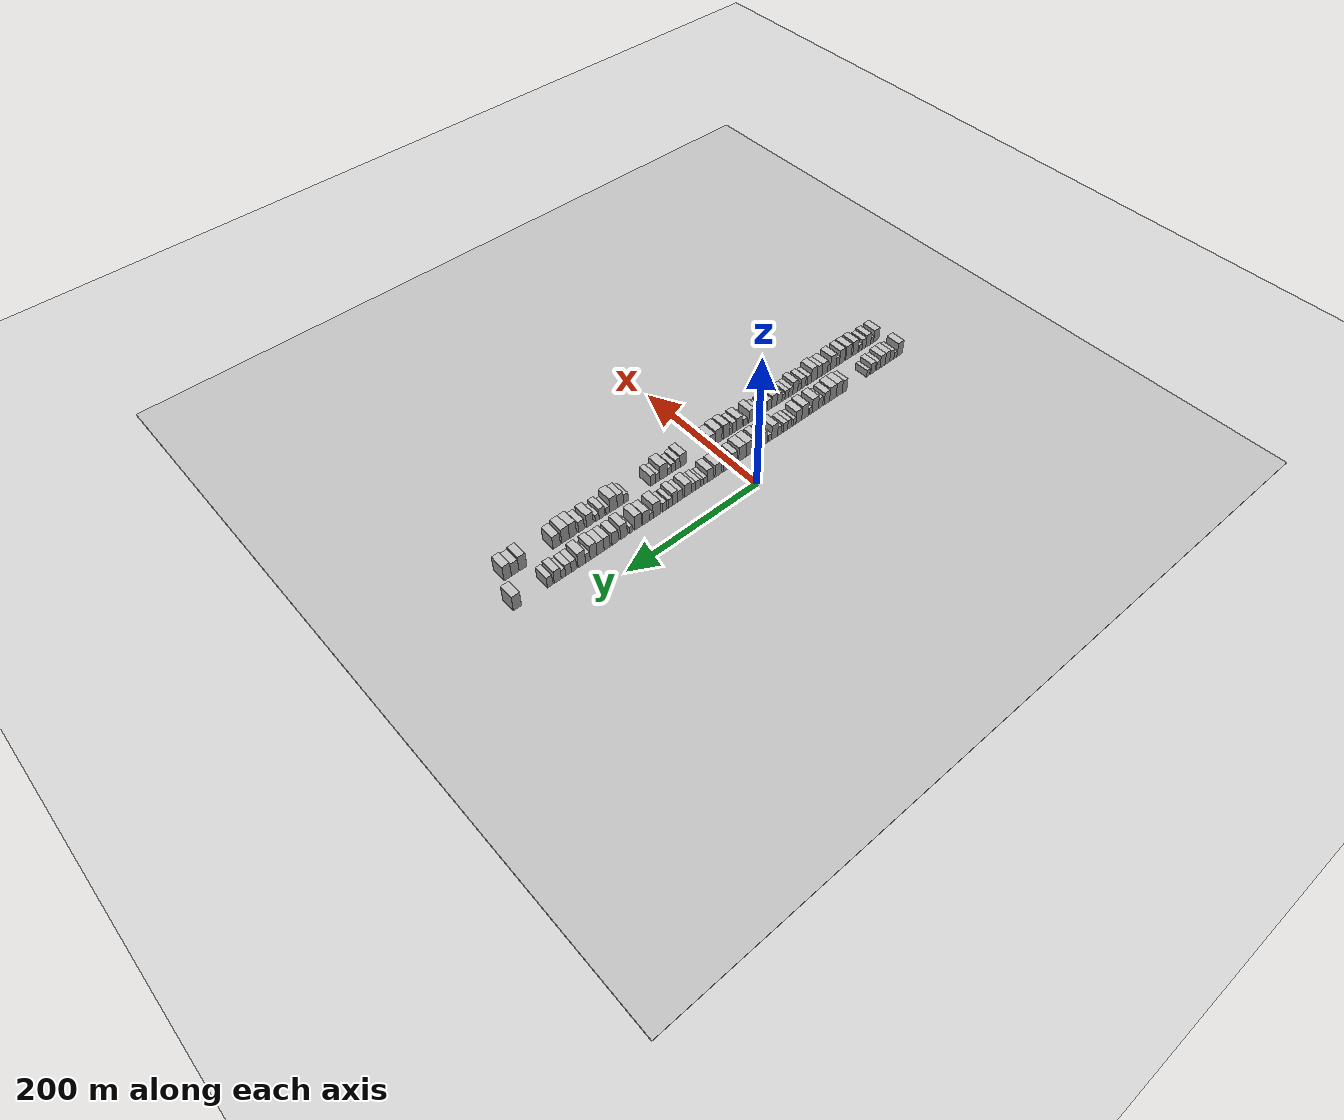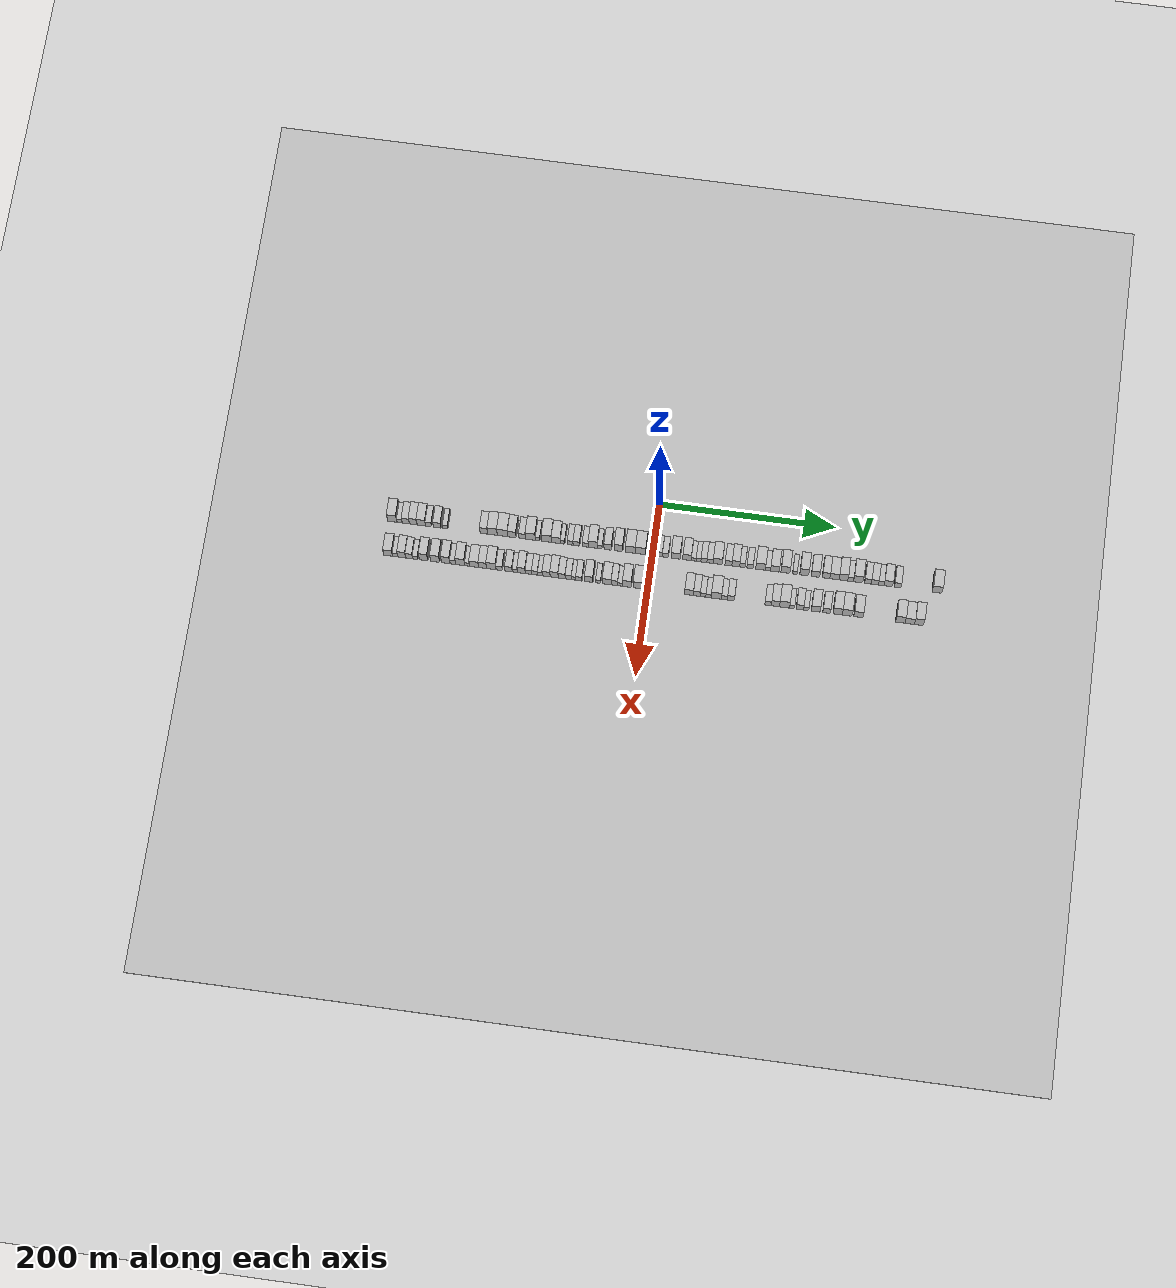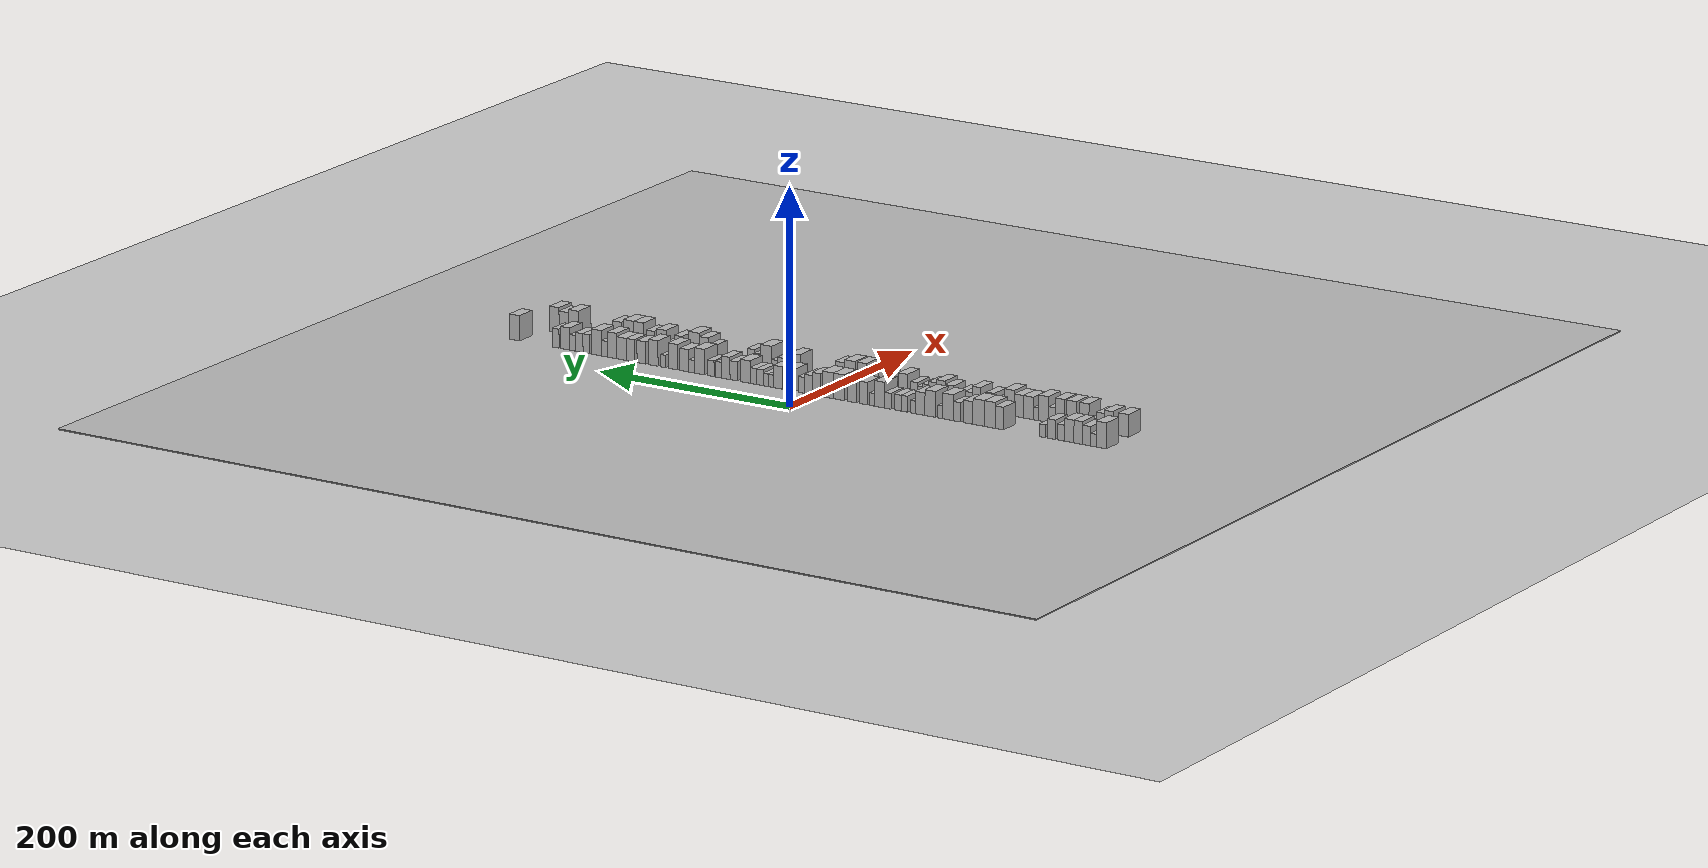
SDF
<?xml version="1.0" encoding="utf-8"?>

<sdf version="1.6">

   <world name="default">

      <gui fullscreen="0">

         <camera name="user_camera">

            <pose>-15 0 4.57585 0 0 0</pose>

            <view_controller>orbit</view_controller>

         </camera>

      </gui>

      <scene>

         <sky>

           <clouds>

             <speed>12</speed>

           </clouds>

         </sky>

         <ambient>0.4 0.4 0.4 1</ambient>

         <background>0.7 0.7 0.7 1</background>

         <shadows>1</shadows>

      </scene>

      <gravity>0 0 -9.8066</gravity>

      <magnetic_field>6e-06 2.3e-05 -4.2e-05</magnetic_field>

      <physics default="0" name="default_physics" type="ode">

         <ode>

            <solver>

               <type>quick</type>

               <iters>10</iters>

               <sor>1.0</sor>

               <use_dynamic_moi_rescaling>0</use_dynamic_moi_rescaling>

            </solver>

            <constraints>

               <cfm>0</cfm>

               <erp>0.2</erp>

               <contact_max_correcting_vel>100</contact_max_correcting_vel>

               <contact_surface_layer>0.001</contact_surface_layer>

            </constraints>

         </ode>

         <max_step_size>0.004</max_step_size>

         <real_time_factor>1</real_time_factor>

         <real_time_update_rate>250</real_time_update_rate>

      </physics>

      <light name="sun" type="directional">

         <cast_shadows>1</cast_shadows>

         <pose>0 0 10 0 0 0</pose>

         <diffuse>0.8 0.8 0.8 1</diffuse>

         <specular>0.2 0.2 0.2 1</specular>

         <attenuation>

            <range>1000</range>

            <constant>0.9</constant>

            <linear>0.01</linear>

            <quadratic>0.001</quadratic>

         </attenuation>

         <direction>-0.5 0.1 -0.9</direction>

      </light>

      <include>

         <name>ground_plane_1</name>

         <uri>model://HANNAS_ground_plane</uri>

         <pose>0 0 0  0 0 0</pose>

      </include>

      <include>

         <name>ground_plane_2</name>

         <uri>model://HANNAS_ground_plane</uri>

         <pose>100 0 0  0 0 0</pose>

      </include>

      <model name="building_1">

         <static>1</static>

         <pose frame="">50.0000 -294.7138 0 0.000000 0.000000 0.000000</pose>

         <link name="link">

            <pose frame="">0 0 12.00 0 0 0</pose>

            <collision name="collision">

               <geometry>

                  <box>

                     <size>20.0000 10.5724 24.0000</size>

                  </box>

               </geometry>

               <max_contacts>10</max_contacts>

               <surface>

                  <contact>

                     <ode/>

                  </contact>

                  <bounce/>

                  <friction>

                     <torsional>

                        <ode/>

                     </torsional>

                     <ode/>

                  </friction>

               </surface>

            </collision>

            <visual name="visual">

               <cast_shadows>0</cast_shadows>

               <geometry>

                  <box>

                     <size>20.0000 10.5724 24.0000</size>

                  </box>

               </geometry>

               <material>

                  <script>

                     <uri>model://HANNAS_wall/materials/scripts</uri>

                     <uri>model://HANNAS_wall/materials/textures</uri>

                     <name>vrc/HANNAS_wall</name>

                  </script>

               </material>

            </visual>

            <self_collide>0</self_collide>

            <enable_wind>0</enable_wind>

            <kinematic>0</kinematic>

         </link>

      </model>

      <model name="building_2">

         <static>1</static>

         <pose frame="">50.0000 -286.5474 0 0.000000 0.000000 0.000000</pose>

         <link name="link">

            <pose frame="">0 0 6.00 0 0 0</pose>

            <collision name="collision">

               <geometry>

                  <box>

                     <size>20.0000 5.7604 12.0000</size>

                  </box>

               </geometry>

               <max_contacts>10</max_contacts>

               <surface>

                  <contact>

                     <ode/>

                  </contact>

                  <bounce/>

                  <friction>

                     <torsional>

                        <ode/>

                     </torsional>

                     <ode/>

                  </friction>

               </surface>

            </collision>

            <visual name="visual">

               <cast_shadows>0</cast_shadows>

               <geometry>

                  <box>

                     <size>20.0000 5.7604 12.0000</size>

                  </box>

               </geometry>

               <material>

                  <script>

                     <uri>model://HANNAS_wall/materials/scripts</uri>

                     <uri>model://HANNAS_wall/materials/textures</uri>

                     <name>vrc/HANNAS_wall</name>

                  </script>

               </material>

            </visual>

            <self_collide>0</self_collide>

            <enable_wind>0</enable_wind>

            <kinematic>0</kinematic>

         </link>

      </model>

      <model name="building_3">

         <static>1</static>

         <pose frame="">50.0000 -279.5543 0 0.000000 0.000000 0.000000</pose>

         <link name="link">

            <pose frame="">0 0 9.00 0 0 0</pose>

            <collision name="collision">

               <geometry>

                  <box>

                     <size>20.0000 8.2259 18.0000</size>

                  </box>

               </geometry>

               <max_contacts>10</max_contacts>

               <surface>

                  <contact>

                     <ode/>

                  </contact>

                  <bounce/>

                  <friction>

                     <torsional>

                        <ode/>

                     </torsional>

                     <ode/>

                  </friction>

               </surface>

            </collision>

            <visual name="visual">

               <cast_shadows>0</cast_shadows>

               <geometry>

                  <box>

                     <size>20.0000 8.2259 18.0000</size>

                  </box>

               </geometry>

               <material>

                  <script>

                     <uri>model://HANNAS_wall/materials/scripts</uri>

                     <uri>model://HANNAS_wall/materials/textures</uri>

                     <name>vrc/HANNAS_wall</name>

                  </script>

               </material>

            </visual>

            <self_collide>0</self_collide>

            <enable_wind>0</enable_wind>

            <kinematic>0</kinematic>

         </link>

      </model>

      <model name="building_4">

         <static>1</static>

         <pose frame="">50.0000 -271.0660 0 0.000000 0.000000 0.000000</pose>

         <link name="link">

            <pose frame="">0 0 10.50 0 0 0</pose>

            <collision name="collision">

               <geometry>

                  <box>

                     <size>20.0000 8.7508 21.0000</size>

                  </box>

               </geometry>

               <max_contacts>10</max_contacts>

               <surface>

                  <contact>

                     <ode/>

                  </contact>

                  <bounce/>

                  <friction>

                     <torsional>

                        <ode/>

                     </torsional>

                     <ode/>

                  </friction>

               </surface>

            </collision>

            <visual name="visual">

               <cast_shadows>0</cast_shadows>

               <geometry>

                  <box>

                     <size>20.0000 8.7508 21.0000</size>

                  </box>

               </geometry>

               <material>

                  <script>

                     <uri>model://HANNAS_wall/materials/scripts</uri>

                     <uri>model://HANNAS_wall/materials/textures</uri>

                     <name>vrc/HANNAS_wall</name>

                  </script>

               </material>

            </visual>

            <self_collide>0</self_collide>

            <enable_wind>0</enable_wind>

            <kinematic>0</kinematic>

         </link>

      </model>

      <model name="building_5">

         <static>1</static>

         <pose frame="">50.0000 -261.7841 0 0.000000 0.000000 0.000000</pose>

         <link name="link">

            <pose frame="">0 0 10.50 0 0 0</pose>

            <collision name="collision">

               <geometry>

                  <box>

                     <size>20.0000 9.8129 21.0000</size>

                  </box>

               </geometry>

               <max_contacts>10</max_contacts>

               <surface>

                  <contact>

                     <ode/>

                  </contact>

                  <bounce/>

                  <friction>

                     <torsional>

                        <ode/>

                     </torsional>

                     <ode/>

                  </friction>

               </surface>

            </collision>

            <visual name="visual">

               <cast_shadows>0</cast_shadows>

               <geometry>

                  <box>

                     <size>20.0000 9.8129 21.0000</size>

                  </box>

               </geometry>

               <material>

                  <script>

                     <uri>model://HANNAS_wall/materials/scripts</uri>

                     <uri>model://HANNAS_wall/materials/textures</uri>

                     <name>vrc/HANNAS_wall</name>

                  </script>

               </material>

            </visual>

            <self_collide>0</self_collide>

            <enable_wind>0</enable_wind>

            <kinematic>0</kinematic>

         </link>

      </model>

      <model name="building_6">

         <static>1</static>

         <pose frame="">50.0000 -253.4980 0 0.000000 0.000000 0.000000</pose>

         <link name="link">

            <pose frame="">0 0 7.50 0 0 0</pose>

            <collision name="collision">

               <geometry>

                  <box>

                     <size>20.0000 6.7593 15.0000</size>

                  </box>

               </geometry>

               <max_contacts>10</max_contacts>

               <surface>

                  <contact>

                     <ode/>

                  </contact>

                  <bounce/>

                  <friction>

                     <torsional>

                        <ode/>

                     </torsional>

                     <ode/>

                  </friction>

               </surface>

            </collision>

            <visual name="visual">

               <cast_shadows>0</cast_shadows>

               <geometry>

                  <box>

                     <size>20.0000 6.7593 15.0000</size>

                  </box>

               </geometry>

               <material>

                  <script>

                     <uri>model://HANNAS_wall/materials/scripts</uri>

                     <uri>model://HANNAS_wall/materials/textures</uri>

                     <name>vrc/HANNAS_wall</name>

                  </script>

               </material>

            </visual>

            <self_collide>0</self_collide>

            <enable_wind>0</enable_wind>

            <kinematic>0</kinematic>

         </link>

      </model>

      <model name="building_7">

         <static>1</static>

         <pose frame="">50.0000 -243.8126 0 0.000000 0.000000 0.000000</pose>

         <link name="link">

            <pose frame="">0 0 9.00 0 0 0</pose>

            <collision name="collision">

               <geometry>

                  <box>

                     <size>20.0000 8.6116 18.0000</size>

                  </box>

               </geometry>

               <max_contacts>10</max_contacts>

               <surface>

                  <contact>

                     <ode/>

                  </contact>

                  <bounce/>

                  <friction>

                     <torsional>

                        <ode/>

                     </torsional>

                     <ode/>

                  </friction>

               </surface>

            </collision>

            <visual name="visual">

               <cast_shadows>0</cast_shadows>

               <geometry>

                  <box>

                     <size>20.0000 8.6116 18.0000</size>

                  </box>

               </geometry>

               <material>

                  <script>

                     <uri>model://HANNAS_wall/materials/scripts</uri>

                     <uri>model://HANNAS_wall/materials/textures</uri>

                     <name>vrc/HANNAS_wall</name>

                  </script>

               </material>

            </visual>

            <self_collide>0</self_collide>

            <enable_wind>0</enable_wind>

            <kinematic>0</kinematic>

         </link>

      </model>

      <model name="building_8">

         <static>1</static>

         <pose frame="">50.0000 -234.6748 0 0.000000 0.000000 0.000000</pose>

         <link name="link">

            <pose frame="">0 0 6.00 0 0 0</pose>

            <collision name="collision">

               <geometry>

                  <box>

                     <size>20.0000 5.6639 12.0000</size>

                  </box>

               </geometry>

               <max_contacts>10</max_contacts>

               <surface>

                  <contact>

                     <ode/>

                  </contact>

                  <bounce/>

                  <friction>

                     <torsional>

                        <ode/>

                     </torsional>

                     <ode/>

                  </friction>

               </surface>

            </collision>

            <visual name="visual">

               <cast_shadows>0</cast_shadows>

               <geometry>

                  <box>

                     <size>20.0000 5.6639 12.0000</size>

                  </box>

               </geometry>

               <material>

                  <script>

                     <uri>model://HANNAS_wall/materials/scripts</uri>

                     <uri>model://HANNAS_wall/materials/textures</uri>

                     <name>vrc/HANNAS_wall</name>

                  </script>

               </material>

            </visual>

            <self_collide>0</self_collide>

            <enable_wind>0</enable_wind>

            <kinematic>0</kinematic>

         </link>

      </model>

      <model name="building_9">

         <static>1</static>

         <pose frame="">50.0000 -190.8144 0 0.000000 0.000000 0.000000</pose>

         <link name="link">

            <pose frame="">0 0 10.50 0 0 0</pose>

            <collision name="collision">

               <geometry>

                  <box>

                     <size>20.0000 8.6856 21.0000</size>

                  </box>

               </geometry>

               <max_contacts>10</max_contacts>

               <surface>

                  <contact>

                     <ode/>

                  </contact>

                  <bounce/>

                  <friction>

                     <torsional>

                        <ode/>

                     </torsional>

                     <ode/>

                  </friction>

               </surface>

            </collision>

            <visual name="visual">

               <cast_shadows>0</cast_shadows>

               <geometry>

                  <box>

                     <size>20.0000 8.6856 21.0000</size>

                  </box>

               </geometry>

               <material>

                  <script>

                     <uri>model://HANNAS_wall/materials/scripts</uri>

                     <uri>model://HANNAS_wall/materials/textures</uri>

                     <name>vrc/HANNAS_wall</name>

                  </script>

               </material>

            </visual>

            <self_collide>0</self_collide>

            <enable_wind>0</enable_wind>

            <kinematic>0</kinematic>

         </link>

      </model>

      <model name="building_10">

         <static>1</static>

         <pose frame="">50.0000 -180.9890 0 0.000000 0.000000 0.000000</pose>

         <link name="link">

            <pose frame="">0 0 12.00 0 0 0</pose>

            <collision name="collision">

               <geometry>

                  <box>

                     <size>20.0000 10.9650 24.0000</size>

                  </box>

               </geometry>

               <max_contacts>10</max_contacts>

               <surface>

                  <contact>

                     <ode/>

                  </contact>

                  <bounce/>

                  <friction>

                     <torsional>

                        <ode/>

                     </torsional>

                     <ode/>

                  </friction>

               </surface>

            </collision>

            <visual name="visual">

               <cast_shadows>0</cast_shadows>

               <geometry>

                  <box>

                     <size>20.0000 10.9650 24.0000</size>

                  </box>

               </geometry>

               <material>

                  <script>

                     <uri>model://HANNAS_wall/materials/scripts</uri>

                     <uri>model://HANNAS_wall/materials/textures</uri>

                     <name>vrc/HANNAS_wall</name>

                  </script>

               </material>

            </visual>

            <self_collide>0</self_collide>

            <enable_wind>0</enable_wind>

            <kinematic>0</kinematic>

         </link>

      </model>

      <model name="building_11">

         <static>1</static>

         <pose frame="">50.0000 -169.5514 0 0.000000 0.000000 0.000000</pose>

         <link name="link">

            <pose frame="">0 0 12.00 0 0 0</pose>

            <collision name="collision">

               <geometry>

                  <box>

                     <size>20.0000 11.9102 24.0000</size>

                  </box>

               </geometry>

               <max_contacts>10</max_contacts>

               <surface>

                  <contact>

                     <ode/>

                  </contact>

                  <bounce/>

                  <friction>

                     <torsional>

                        <ode/>

                     </torsional>

                     <ode/>

                  </friction>

               </surface>

            </collision>

            <visual name="visual">

               <cast_shadows>0</cast_shadows>

               <geometry>

                  <box>

                     <size>20.0000 11.9102 24.0000</size>

                  </box>

               </geometry>

               <material>

                  <script>

                     <uri>model://HANNAS_wall/materials/scripts</uri>

                     <uri>model://HANNAS_wall/materials/textures</uri>

                     <name>vrc/HANNAS_wall</name>

                  </script>

               </material>

            </visual>

            <self_collide>0</self_collide>

            <enable_wind>0</enable_wind>

            <kinematic>0</kinematic>

         </link>

      </model>

      <model name="building_12">

         <static>1</static>

         <pose frame="">50.0000 -158.8469 0 0.000000 0.000000 0.000000</pose>

         <link name="link">

            <pose frame="">0 0 10.50 0 0 0</pose>

            <collision name="collision">

               <geometry>

                  <box>

                     <size>20.0000 9.4989 21.0000</size>

                  </box>

               </geometry>

               <max_contacts>10</max_contacts>

               <surface>

                  <contact>

                     <ode/>

                  </contact>

                  <bounce/>

                  <friction>

                     <torsional>

                        <ode/>

                     </torsional>

                     <ode/>

                  </friction>

               </surface>

            </collision>

            <visual name="visual">

               <cast_shadows>0</cast_shadows>

               <geometry>

                  <box>

                     <size>20.0000 9.4989 21.0000</size>

                  </box>

               </geometry>

               <material>

                  <script>

                     <uri>model://HANNAS_wall/materials/scripts</uri>

                     <uri>model://HANNAS_wall/materials/textures</uri>

                     <name>vrc/HANNAS_wall</name>

                  </script>

               </material>

            </visual>

            <self_collide>0</self_collide>

            <enable_wind>0</enable_wind>

            <kinematic>0</kinematic>

         </link>

      </model>

      <model name="building_13">

         <static>1</static>

         <pose frame="">50.0000 -147.2973 0 0.000000 0.000000 0.000000</pose>

         <link name="link">

            <pose frame="">0 0 9.00 0 0 0</pose>

            <collision name="collision">

               <geometry>

                  <box>

                     <size>20.0000 7.6004 18.0000</size>

                  </box>

               </geometry>

               <max_contacts>10</max_contacts>

               <surface>

                  <contact>

                     <ode/>

                  </contact>

                  <bounce/>

                  <friction>

                     <torsional>

                        <ode/>

                     </torsional>

                     <ode/>

                  </friction>

               </surface>

            </collision>

            <visual name="visual">

               <cast_shadows>0</cast_shadows>

               <geometry>

                  <box>

                     <size>20.0000 7.6004 18.0000</size>

                  </box>

               </geometry>

               <material>

                  <script>

                     <uri>model://HANNAS_wall/materials/scripts</uri>

                     <uri>model://HANNAS_wall/materials/textures</uri>

                     <name>vrc/HANNAS_wall</name>

                  </script>

               </material>

            </visual>

            <self_collide>0</self_collide>

            <enable_wind>0</enable_wind>

            <kinematic>0</kinematic>

         </link>

      </model>

      <model name="building_14">

         <static>1</static>

         <pose frame="">50.0000 -137.9208 0 0.000000 0.000000 0.000000</pose>

         <link name="link">

            <pose frame="">0 0 12.00 0 0 0</pose>

            <collision name="collision">

               <geometry>

                  <box>

                     <size>20.0000 11.1527 24.0000</size>

                  </box>

               </geometry>

               <max_contacts>10</max_contacts>

               <surface>

                  <contact>

                     <ode/>

                  </contact>

                  <bounce/>

                  <friction>

                     <torsional>

                        <ode/>

                     </torsional>

                     <ode/>

                  </friction>

               </surface>

            </collision>

            <visual name="visual">

               <cast_shadows>0</cast_shadows>

               <geometry>

                  <box>

                     <size>20.0000 11.1527 24.0000</size>

                  </box>

               </geometry>

               <material>

                  <script>

                     <uri>model://HANNAS_wall/materials/scripts</uri>

                     <uri>model://HANNAS_wall/materials/textures</uri>

                     <name>vrc/HANNAS_wall</name>

                  </script>

               </material>

            </visual>

            <self_collide>0</self_collide>

            <enable_wind>0</enable_wind>

            <kinematic>0</kinematic>

         </link>

      </model>

      <model name="building_15">

         <static>1</static>

         <pose frame="">50.0000 -129.8487 0 0.000000 0.000000 0.000000</pose>

         <link name="link">

            <pose frame="">0 0 6.00 0 0 0</pose>

            <collision name="collision">

               <geometry>

                  <box>

                     <size>20.0000 4.9914 12.0000</size>

                  </box>

               </geometry>

               <max_contacts>10</max_contacts>

               <surface>

                  <contact>

                     <ode/>

                  </contact>

                  <bounce/>

                  <friction>

                     <torsional>

                        <ode/>

                     </torsional>

                     <ode/>

                  </friction>

               </surface>

            </collision>

            <visual name="visual">

               <cast_shadows>0</cast_shadows>

               <geometry>

                  <box>

                     <size>20.0000 4.9914 12.0000</size>

                  </box>

               </geometry>

               <material>

                  <script>

                     <uri>model://HANNAS_wall/materials/scripts</uri>

                     <uri>model://HANNAS_wall/materials/textures</uri>

                     <name>vrc/HANNAS_wall</name>

                  </script>

               </material>

            </visual>

            <self_collide>0</self_collide>

            <enable_wind>0</enable_wind>

            <kinematic>0</kinematic>

         </link>

      </model>

      <model name="building_16">

         <static>1</static>

         <pose frame="">50.0000 -119.7771 0 0.000000 0.000000 0.000000</pose>

         <link name="link">

            <pose frame="">0 0 12.00 0 0 0</pose>

            <collision name="collision">

               <geometry>

                  <box>

                     <size>20.0000 11.1517 24.0000</size>

                  </box>

               </geometry>

               <max_contacts>10</max_contacts>

               <surface>

                  <contact>

                     <ode/>

                  </contact>

                  <bounce/>

                  <friction>

                     <torsional>

                        <ode/>

                     </torsional>

                     <ode/>

                  </friction>

               </surface>

            </collision>

            <visual name="visual">

               <cast_shadows>0</cast_shadows>

               <geometry>

                  <box>

                     <size>20.0000 11.1517 24.0000</size>

                  </box>

               </geometry>

               <material>

                  <script>

                     <uri>model://HANNAS_wall/materials/scripts</uri>

                     <uri>model://HANNAS_wall/materials/textures</uri>

                     <name>vrc/HANNAS_wall</name>

                  </script>

               </material>

            </visual>

            <self_collide>0</self_collide>

            <enable_wind>0</enable_wind>

            <kinematic>0</kinematic>

         </link>

      </model>

      <model name="building_17">

         <static>1</static>

         <pose frame="">50.0000 -109.1579 0 0.000000 0.000000 0.000000</pose>

         <link name="link">

            <pose frame="">0 0 10.50 0 0 0</pose>

            <collision name="collision">

               <geometry>

                  <box>

                     <size>20.0000 10.0868 21.0000</size>

                  </box>

               </geometry>

               <max_contacts>10</max_contacts>

               <surface>

                  <contact>

                     <ode/>

                  </contact>

                  <bounce/>

                  <friction>

                     <torsional>

                        <ode/>

                     </torsional>

                     <ode/>

                  </friction>

               </surface>

            </collision>

            <visual name="visual">

               <cast_shadows>0</cast_shadows>

               <geometry>

                  <box>

                     <size>20.0000 10.0868 21.0000</size>

                  </box>

               </geometry>

               <material>

                  <script>

                     <uri>model://HANNAS_wall/materials/scripts</uri>

                     <uri>model://HANNAS_wall/materials/textures</uri>

                     <name>vrc/HANNAS_wall</name>

                  </script>

               </material>

            </visual>

            <self_collide>0</self_collide>

            <enable_wind>0</enable_wind>

            <kinematic>0</kinematic>

         </link>

      </model>

      <model name="building_18">

         <static>1</static>

         <pose frame="">50.0000 -101.6478 0 0.000000 0.000000 0.000000</pose>

         <link name="link">

            <pose frame="">0 0 6.00 0 0 0</pose>

            <collision name="collision">

               <geometry>

                  <box>

                     <size>20.0000 4.9333 12.0000</size>

                  </box>

               </geometry>

               <max_contacts>10</max_contacts>

               <surface>

                  <contact>

                     <ode/>

                  </contact>

                  <bounce/>

                  <friction>

                     <torsional>

                        <ode/>

                     </torsional>

                     <ode/>

                  </friction>

               </surface>

            </collision>

            <visual name="visual">

               <cast_shadows>0</cast_shadows>

               <geometry>

                  <box>

                     <size>20.0000 4.9333 12.0000</size>

                  </box>

               </geometry>

               <material>

                  <script>

                     <uri>model://HANNAS_wall/materials/scripts</uri>

                     <uri>model://HANNAS_wall/materials/textures</uri>

                     <name>vrc/HANNAS_wall</name>

                  </script>

               </material>

            </visual>

            <self_collide>0</self_collide>

            <enable_wind>0</enable_wind>

            <kinematic>0</kinematic>

         </link>

      </model>

      <model name="building_19">

         <static>1</static>

         <pose frame="">50.0000 -92.9845 0 0.000000 0.000000 0.000000</pose>

         <link name="link">

            <pose frame="">0 0 7.50 0 0 0</pose>

            <collision name="collision">

               <geometry>

                  <box>

                     <size>20.0000 6.3934 15.0000</size>

                  </box>

               </geometry>

               <max_contacts>10</max_contacts>

               <surface>

                  <contact>

                     <ode/>

                  </contact>

                  <bounce/>

                  <friction>

                     <torsional>

                        <ode/>

                     </torsional>

                     <ode/>

                  </friction>

               </surface>

            </collision>

            <visual name="visual">

               <cast_shadows>0</cast_shadows>

               <geometry>

                  <box>

                     <size>20.0000 6.3934 15.0000</size>

                  </box>

               </geometry>

               <material>

                  <script>

                     <uri>model://HANNAS_wall/materials/scripts</uri>

                     <uri>model://HANNAS_wall/materials/textures</uri>

                     <name>vrc/HANNAS_wall</name>

                  </script>

               </material>

            </visual>

            <self_collide>0</self_collide>

            <enable_wind>0</enable_wind>

            <kinematic>0</kinematic>

         </link>

      </model>

      <model name="building_20">

         <static>1</static>

         <pose frame="">50.0000 -86.0525 0 0.000000 0.000000 0.000000</pose>

         <link name="link">

            <pose frame="">0 0 7.50 0 0 0</pose>

            <collision name="collision">

               <geometry>

                  <box>

                     <size>20.0000 7.4705 15.0000</size>

                  </box>

               </geometry>

               <max_contacts>10</max_contacts>

               <surface>

                  <contact>

                     <ode/>

                  </contact>

                  <bounce/>

                  <friction>

                     <torsional>

                        <ode/>

                     </torsional>

                     <ode/>

                  </friction>

               </surface>

            </collision>

            <visual name="visual">

               <cast_shadows>0</cast_shadows>

               <geometry>

                  <box>

                     <size>20.0000 7.4705 15.0000</size>

                  </box>

               </geometry>

               <material>

                  <script>

                     <uri>model://HANNAS_wall/materials/scripts</uri>

                     <uri>model://HANNAS_wall/materials/textures</uri>

                     <name>vrc/HANNAS_wall</name>

                  </script>

               </material>

            </visual>

            <self_collide>0</self_collide>

            <enable_wind>0</enable_wind>

            <kinematic>0</kinematic>

         </link>

      </model>

      <model name="building_21">

         <static>1</static>

         <pose frame="">50.0000 -75.9563 0 0.000000 0.000000 0.000000</pose>

         <link name="link">

            <pose frame="">0 0 7.50 0 0 0</pose>

            <collision name="collision">

               <geometry>

                  <box>

                     <size>20.0000 6.7220 15.0000</size>

                  </box>

               </geometry>

               <max_contacts>10</max_contacts>

               <surface>

                  <contact>

                     <ode/>

                  </contact>

                  <bounce/>

                  <friction>

                     <torsional>

                        <ode/>

                     </torsional>

                     <ode/>

                  </friction>

               </surface>

            </collision>

            <visual name="visual">

               <cast_shadows>0</cast_shadows>

               <geometry>

                  <box>

                     <size>20.0000 6.7220 15.0000</size>

                  </box>

               </geometry>

               <material>

                  <script>

                     <uri>model://HANNAS_wall/materials/scripts</uri>

                     <uri>model://HANNAS_wall/materials/textures</uri>

                     <name>vrc/HANNAS_wall</name>

                  </script>

               </material>

            </visual>

            <self_collide>0</self_collide>

            <enable_wind>0</enable_wind>

            <kinematic>0</kinematic>

         </link>

      </model>

      <model name="building_22">

         <static>1</static>

         <pose frame="">50.0000 -67.4464 0 0.000000 0.000000 0.000000</pose>

         <link name="link">

            <pose frame="">0 0 12.00 0 0 0</pose>

            <collision name="collision">

               <geometry>

                  <box>

                     <size>20.0000 10.2976 24.0000</size>

                  </box>

               </geometry>

               <max_contacts>10</max_contacts>

               <surface>

                  <contact>

                     <ode/>

                  </contact>

                  <bounce/>

                  <friction>

                     <torsional>

                        <ode/>

                     </torsional>

                     <ode/>

                  </friction>

               </surface>

            </collision>

            <visual name="visual">

               <cast_shadows>0</cast_shadows>

               <geometry>

                  <box>

                     <size>20.0000 10.2976 24.0000</size>

                  </box>

               </geometry>

               <material>

                  <script>

                     <uri>model://HANNAS_wall/materials/scripts</uri>

                     <uri>model://HANNAS_wall/materials/textures</uri>

                     <name>vrc/HANNAS_wall</name>

                  </script>

               </material>

            </visual>

            <self_collide>0</self_collide>

            <enable_wind>0</enable_wind>

            <kinematic>0</kinematic>

         </link>

      </model>

      <model name="building_23">

         <static>1</static>

         <pose frame="">50.0000 -59.5560 0 0.000000 0.000000 0.000000</pose>

         <link name="link">

            <pose frame="">0 0 6.00 0 0 0</pose>

            <collision name="collision">

               <geometry>

                  <box>

                     <size>20.0000 5.4833 12.0000</size>

                  </box>

               </geometry>

               <max_contacts>10</max_contacts>

               <surface>

                  <contact>

                     <ode/>

                  </contact>

                  <bounce/>

                  <friction>

                     <torsional>

                        <ode/>

                     </torsional>

                     <ode/>

                  </friction>

               </surface>

            </collision>

            <visual name="visual">

               <cast_shadows>0</cast_shadows>

               <geometry>

                  <box>

                     <size>20.0000 5.4833 12.0000</size>

                  </box>

               </geometry>

               <material>

                  <script>

                     <uri>model://HANNAS_wall/materials/scripts</uri>

                     <uri>model://HANNAS_wall/materials/textures</uri>

                     <name>vrc/HANNAS_wall</name>

                  </script>

               </material>

            </visual>

            <self_collide>0</self_collide>

            <enable_wind>0</enable_wind>

            <kinematic>0</kinematic>

         </link>

      </model>

      <model name="building_24">

         <static>1</static>

         <pose frame="">50.0000 -50.5672 0 0.000000 0.000000 0.000000</pose>

         <link name="link">

            <pose frame="">0 0 10.50 0 0 0</pose>

            <collision name="collision">

               <geometry>

                  <box>

                     <size>20.0000 8.4941 21.0000</size>

                  </box>

               </geometry>

               <max_contacts>10</max_contacts>

               <surface>

                  <contact>

                     <ode/>

                  </contact>

                  <bounce/>

                  <friction>

                     <torsional>

                        <ode/>

                     </torsional>

                     <ode/>

                  </friction>

               </surface>

            </collision>

            <visual name="visual">

               <cast_shadows>0</cast_shadows>

               <geometry>

                  <box>

                     <size>20.0000 8.4941 21.0000</size>

                  </box>

               </geometry>

               <material>

                  <script>

                     <uri>model://HANNAS_wall/materials/scripts</uri>

                     <uri>model://HANNAS_wall/materials/textures</uri>

                     <name>vrc/HANNAS_wall</name>

                  </script>

               </material>

            </visual>

            <self_collide>0</self_collide>

            <enable_wind>0</enable_wind>

            <kinematic>0</kinematic>

         </link>

      </model>

      <model name="building_25">

         <static>1</static>

         <pose frame="">50.0000 -38.4495 0 0.000000 0.000000 0.000000</pose>

         <link name="link">

            <pose frame="">0 0 12.00 0 0 0</pose>

            <collision name="collision">

               <geometry>

                  <box>

                     <size>20.0000 9.7414 24.0000</size>

                  </box>

               </geometry>

               <max_contacts>10</max_contacts>

               <surface>

                  <contact>

                     <ode/>

                  </contact>

                  <bounce/>

                  <friction>

                     <torsional>

                        <ode/>

                     </torsional>

                     <ode/>

                  </friction>

               </surface>

            </collision>

            <visual name="visual">

               <cast_shadows>0</cast_shadows>

               <geometry>

                  <box>

                     <size>20.0000 9.7414 24.0000</size>

                  </box>

               </geometry>

               <material>

                  <script>

                     <uri>model://HANNAS_wall/materials/scripts</uri>

                     <uri>model://HANNAS_wall/materials/textures</uri>

                     <name>vrc/HANNAS_wall</name>

                  </script>

               </material>

            </visual>

            <self_collide>0</self_collide>

            <enable_wind>0</enable_wind>

            <kinematic>0</kinematic>

         </link>

      </model>

      <model name="building_26">

         <static>1</static>

         <pose frame="">50.0000 -24.9672 0 0.000000 0.000000 0.000000</pose>

         <link name="link">

            <pose frame="">0 0 12.00 0 0 0</pose>

            <collision name="collision">

               <geometry>

                  <box>

                     <size>20.0000 11.2231 24.0000</size>

                  </box>

               </geometry>

               <max_contacts>10</max_contacts>

               <surface>

                  <contact>

                     <ode/>

                  </contact>

                  <bounce/>

                  <friction>

                     <torsional>

                        <ode/>

                     </torsional>

                     <ode/>

                  </friction>

               </surface>

            </collision>

            <visual name="visual">

               <cast_shadows>0</cast_shadows>

               <geometry>

                  <box>

                     <size>20.0000 11.2231 24.0000</size>

                  </box>

               </geometry>

               <material>

                  <script>

                     <uri>model://HANNAS_wall/materials/scripts</uri>

                     <uri>model://HANNAS_wall/materials/textures</uri>

                     <name>vrc/HANNAS_wall</name>

                  </script>

               </material>

            </visual>

            <self_collide>0</self_collide>

            <enable_wind>0</enable_wind>

            <kinematic>0</kinematic>

         </link>

      </model>

      <model name="building_27">

         <static>1</static>

         <pose frame="">50.0000 -13.4424 0 0.000000 0.000000 0.000000</pose>

         <link name="link">

            <pose frame="">0 0 12.00 0 0 0</pose>

            <collision name="collision">

               <geometry>

                  <box>

                     <size>20.0000 11.8265 24.0000</size>

                  </box>

               </geometry>

               <max_contacts>10</max_contacts>

               <surface>

                  <contact>

                     <ode/>

                  </contact>

                  <bounce/>

                  <friction>

                     <torsional>

                        <ode/>

                     </torsional>

                     <ode/>

                  </friction>

               </surface>

            </collision>

            <visual name="visual">

               <cast_shadows>0</cast_shadows>

               <geometry>

                  <box>

                     <size>20.0000 11.8265 24.0000</size>

                  </box>

               </geometry>

               <material>

                  <script>

                     <uri>model://HANNAS_wall/materials/scripts</uri>

                     <uri>model://HANNAS_wall/materials/textures</uri>

                     <name>vrc/HANNAS_wall</name>

                  </script>

               </material>

            </visual>

            <self_collide>0</self_collide>

            <enable_wind>0</enable_wind>

            <kinematic>0</kinematic>

         </link>

      </model>

      <model name="building_28">

         <static>1</static>

         <pose frame="">50.0000 -1.2540 0 0.000000 0.000000 0.000000</pose>

         <link name="link">

            <pose frame="">0 0 10.50 0 0 0</pose>

            <collision name="collision">

               <geometry>

                  <box>

                     <size>20.0000 8.5501 21.0000</size>

                  </box>

               </geometry>

               <max_contacts>10</max_contacts>

               <surface>

                  <contact>

                     <ode/>

                  </contact>

                  <bounce/>

                  <friction>

                     <torsional>

                        <ode/>

                     </torsional>

                     <ode/>

                  </friction>

               </surface>

            </collision>

            <visual name="visual">

               <cast_shadows>0</cast_shadows>

               <geometry>

                  <box>

                     <size>20.0000 8.5501 21.0000</size>

                  </box>

               </geometry>

               <material>

                  <script>

                     <uri>model://HANNAS_wall/materials/scripts</uri>

                     <uri>model://HANNAS_wall/materials/textures</uri>

                     <name>vrc/HANNAS_wall</name>

                  </script>

               </material>

            </visual>

            <self_collide>0</self_collide>

            <enable_wind>0</enable_wind>

            <kinematic>0</kinematic>

         </link>

      </model>

      <model name="building_29">

         <static>1</static>

         <pose frame="">50.0000 7.0445 0 0.000000 0.000000 0.000000</pose>

         <link name="link">

            <pose frame="">0 0 9.00 0 0 0</pose>

            <collision name="collision">

               <geometry>

                  <box>

                     <size>20.0000 8.0470 18.0000</size>

                  </box>

               </geometry>

               <max_contacts>10</max_contacts>

               <surface>

                  <contact>

                     <ode/>

                  </contact>

                  <bounce/>

                  <friction>

                     <torsional>

                        <ode/>

                     </torsional>

                     <ode/>

                  </friction>

               </surface>

            </collision>

            <visual name="visual">

               <cast_shadows>0</cast_shadows>

               <geometry>

                  <box>

                     <size>20.0000 8.0470 18.0000</size>

                  </box>

               </geometry>

               <material>

                  <script>

                     <uri>model://HANNAS_wall/materials/scripts</uri>

                     <uri>model://HANNAS_wall/materials/textures</uri>

                     <name>vrc/HANNAS_wall</name>

                  </script>

               </material>

            </visual>

            <self_collide>0</self_collide>

            <enable_wind>0</enable_wind>

            <kinematic>0</kinematic>

         </link>

      </model>

      <model name="building_30">

         <static>1</static>

         <pose frame="">50.0000 14.4716 0 0.000000 0.000000 0.000000</pose>

         <link name="link">

            <pose frame="">0 0 7.50 0 0 0</pose>

            <collision name="collision">

               <geometry>

                  <box>

                     <size>20.0000 6.8073 15.0000</size>

                  </box>

               </geometry>

               <max_contacts>10</max_contacts>

               <surface>

                  <contact>

                     <ode/>

                  </contact>

                  <bounce/>

                  <friction>

                     <torsional>

                        <ode/>

                     </torsional>

                     <ode/>

                  </friction>

               </surface>

            </collision>

            <visual name="visual">

               <cast_shadows>0</cast_shadows>

               <geometry>

                  <box>

                     <size>20.0000 6.8073 15.0000</size>

                  </box>

               </geometry>

               <material>

                  <script>

                     <uri>model://HANNAS_wall/materials/scripts</uri>

                     <uri>model://HANNAS_wall/materials/textures</uri>

                     <name>vrc/HANNAS_wall</name>

                  </script>

               </material>

            </visual>

            <self_collide>0</self_collide>

            <enable_wind>0</enable_wind>

            <kinematic>0</kinematic>

         </link>

      </model>

      <model name="building_31">

         <static>1</static>

         <pose frame="">50.0000 26.0191 0 0.000000 0.000000 0.000000</pose>

         <link name="link">

            <pose frame="">0 0 10.50 0 0 0</pose>

            <collision name="collision">

               <geometry>

                  <box>

                     <size>20.0000 10.2875 21.0000</size>

                  </box>

               </geometry>

               <max_contacts>10</max_contacts>

               <surface>

                  <contact>

                     <ode/>

                  </contact>

                  <bounce/>

                  <friction>

                     <torsional>

                        <ode/>

                     </torsional>

                     <ode/>

                  </friction>

               </surface>

            </collision>

            <visual name="visual">

               <cast_shadows>0</cast_shadows>

               <geometry>

                  <box>

                     <size>20.0000 10.2875 21.0000</size>

                  </box>

               </geometry>

               <material>

                  <script>

                     <uri>model://HANNAS_wall/materials/scripts</uri>

                     <uri>model://HANNAS_wall/materials/textures</uri>

                     <name>vrc/HANNAS_wall</name>

                  </script>

               </material>

            </visual>

            <self_collide>0</self_collide>

            <enable_wind>0</enable_wind>

            <kinematic>0</kinematic>

         </link>

      </model>

      <model name="building_32">

         <static>1</static>

         <pose frame="">50.0000 38.9282 0 0.000000 0.000000 0.000000</pose>

         <link name="link">

            <pose frame="">0 0 10.50 0 0 0</pose>

            <collision name="collision">

               <geometry>

                  <box>

                     <size>20.0000 9.5307 21.0000</size>

                  </box>

               </geometry>

               <max_contacts>10</max_contacts>

               <surface>

                  <contact>

                     <ode/>

                  </contact>

                  <bounce/>

                  <friction>

                     <torsional>

                        <ode/>

                     </torsional>

                     <ode/>

                  </friction>

               </surface>

            </collision>

            <visual name="visual">

               <cast_shadows>0</cast_shadows>

               <geometry>

                  <box>

                     <size>20.0000 9.5307 21.0000</size>

                  </box>

               </geometry>

               <material>

                  <script>

                     <uri>model://HANNAS_wall/materials/scripts</uri>

                     <uri>model://HANNAS_wall/materials/textures</uri>

                     <name>vrc/HANNAS_wall</name>

                  </script>

               </material>

            </visual>

            <self_collide>0</self_collide>

            <enable_wind>0</enable_wind>

            <kinematic>0</kinematic>

         </link>

      </model>

      <model name="building_33">

         <static>1</static>

         <pose frame="">50.0000 46.4095 0 0.000000 0.000000 0.000000</pose>

         <link name="link">

            <pose frame="">0 0 6.00 0 0 0</pose>

            <collision name="collision">

               <geometry>

                  <box>

                     <size>20.0000 5.4320 12.0000</size>

                  </box>

               </geometry>

               <max_contacts>10</max_contacts>

               <surface>

                  <contact>

                     <ode/>

                  </contact>

                  <bounce/>

                  <friction>

                     <torsional>

                        <ode/>

                     </torsional>

                     <ode/>

                  </friction>

               </surface>

            </collision>

            <visual name="visual">

               <cast_shadows>0</cast_shadows>

               <geometry>

                  <box>

                     <size>20.0000 5.4320 12.0000</size>

                  </box>

               </geometry>

               <material>

                  <script>

                     <uri>model://HANNAS_wall/materials/scripts</uri>

                     <uri>model://HANNAS_wall/materials/textures</uri>

                     <name>vrc/HANNAS_wall</name>

                  </script>

               </material>

            </visual>

            <self_collide>0</self_collide>

            <enable_wind>0</enable_wind>

            <kinematic>0</kinematic>

         </link>

      </model>

      <model name="building_34">

         <static>1</static>

         <pose frame="">50.0000 51.8343 0 0.000000 0.000000 0.000000</pose>

         <link name="link">

            <pose frame="">0 0 6.00 0 0 0</pose>

            <collision name="collision">

               <geometry>

                  <box>

                     <size>20.0000 5.4175 12.0000</size>

                  </box>

               </geometry>

               <max_contacts>10</max_contacts>

               <surface>

                  <contact>

                     <ode/>

                  </contact>

                  <bounce/>

                  <friction>

                     <torsional>

                        <ode/>

                     </torsional>

                     <ode/>

                  </friction>

               </surface>

            </collision>

            <visual name="visual">

               <cast_shadows>0</cast_shadows>

               <geometry>

                  <box>

                     <size>20.0000 5.4175 12.0000</size>

                  </box>

               </geometry>

               <material>

                  <script>

                     <uri>model://HANNAS_wall/materials/scripts</uri>

                     <uri>model://HANNAS_wall/materials/textures</uri>

                     <name>vrc/HANNAS_wall</name>

                  </script>

               </material>

            </visual>

            <self_collide>0</self_collide>

            <enable_wind>0</enable_wind>

            <kinematic>0</kinematic>

         </link>

      </model>

      <model name="building_35">

         <static>1</static>

         <pose frame="">50.0000 57.9451 0 0.000000 0.000000 0.000000</pose>

         <link name="link">

            <pose frame="">0 0 7.50 0 0 0</pose>

            <collision name="collision">

               <geometry>

                  <box>

                     <size>20.0000 6.8042 15.0000</size>

                  </box>

               </geometry>

               <max_contacts>10</max_contacts>

               <surface>

                  <contact>

                     <ode/>

                  </contact>

                  <bounce/>

                  <friction>

                     <torsional>

                        <ode/>

                     </torsional>

                     <ode/>

                  </friction>

               </surface>

            </collision>

            <visual name="visual">

               <cast_shadows>0</cast_shadows>

               <geometry>

                  <box>

                     <size>20.0000 6.8042 15.0000</size>

                  </box>

               </geometry>

               <material>

                  <script>

                     <uri>model://HANNAS_wall/materials/scripts</uri>

                     <uri>model://HANNAS_wall/materials/textures</uri>

                     <name>vrc/HANNAS_wall</name>

                  </script>

               </material>

            </visual>

            <self_collide>0</self_collide>

            <enable_wind>0</enable_wind>

            <kinematic>0</kinematic>

         </link>

      </model>

      <model name="building_36">

         <static>1</static>

         <pose frame="">50.0000 64.7987 0 0.000000 0.000000 0.000000</pose>

         <link name="link">

            <pose frame="">0 0 7.50 0 0 0</pose>

            <collision name="collision">

               <geometry>

                  <box>

                     <size>20.0000 6.9030 15.0000</size>

                  </box>

               </geometry>

               <max_contacts>10</max_contacts>

               <surface>

                  <contact>

                     <ode/>

                  </contact>

                  <bounce/>

                  <friction>

                     <torsional>

                        <ode/>

                     </torsional>

                     <ode/>

                  </friction>

               </surface>

            </collision>

            <visual name="visual">

               <cast_shadows>0</cast_shadows>

               <geometry>

                  <box>

                     <size>20.0000 6.9030 15.0000</size>

                  </box>

               </geometry>

               <material>

                  <script>

                     <uri>model://HANNAS_wall/materials/scripts</uri>

                     <uri>model://HANNAS_wall/materials/textures</uri>

                     <name>vrc/HANNAS_wall</name>

                  </script>

               </material>

            </visual>

            <self_collide>0</self_collide>

            <enable_wind>0</enable_wind>

            <kinematic>0</kinematic>

         </link>

      </model>

      <model name="building_37">

         <static>1</static>

         <pose frame="">50.0000 73.4553 0 0.000000 0.000000 0.000000</pose>

         <link name="link">

            <pose frame="">0 0 10.50 0 0 0</pose>

            <collision name="collision">

               <geometry>

                  <box>

                     <size>20.0000 10.4101 21.0000</size>

                  </box>

               </geometry>

               <max_contacts>10</max_contacts>

               <surface>

                  <contact>

                     <ode/>

                  </contact>

                  <bounce/>

                  <friction>

                     <torsional>

                        <ode/>

                     </torsional>

                     <ode/>

                  </friction>

               </surface>

            </collision>

            <visual name="visual">

               <cast_shadows>0</cast_shadows>

               <geometry>

                  <box>

                     <size>20.0000 10.4101 21.0000</size>

                  </box>

               </geometry>

               <material>

                  <script>

                     <uri>model://HANNAS_wall/materials/scripts</uri>

                     <uri>model://HANNAS_wall/materials/textures</uri>

                     <name>vrc/HANNAS_wall</name>

                  </script>

               </material>

            </visual>

            <self_collide>0</self_collide>

            <enable_wind>0</enable_wind>

            <kinematic>0</kinematic>

         </link>

      </model>

      <model name="building_38">

         <static>1</static>

         <pose frame="">50.0000 85.5674 0 0.000000 0.000000 0.000000</pose>

         <link name="link">

            <pose frame="">0 0 9.00 0 0 0</pose>

            <collision name="collision">

               <geometry>

                  <box>

                     <size>20.0000 7.8140 18.0000</size>

                  </box>

               </geometry>

               <max_contacts>10</max_contacts>

               <surface>

                  <contact>

                     <ode/>

                  </contact>

                  <bounce/>

                  <friction>

                     <torsional>

                        <ode/>

                     </torsional>

                     <ode/>

                  </friction>

               </surface>

            </collision>

            <visual name="visual">

               <cast_shadows>0</cast_shadows>

               <geometry>

                  <box>

                     <size>20.0000 7.8140 18.0000</size>

                  </box>

               </geometry>

               <material>

                  <script>

                     <uri>model://HANNAS_wall/materials/scripts</uri>

                     <uri>model://HANNAS_wall/materials/textures</uri>

                     <name>vrc/HANNAS_wall</name>

                  </script>

               </material>

            </visual>

            <self_collide>0</self_collide>

            <enable_wind>0</enable_wind>

            <kinematic>0</kinematic>

         </link>

      </model>

      <model name="building_39">

         <static>1</static>

         <pose frame="">50.0000 93.9009 0 0.000000 0.000000 0.000000</pose>

         <link name="link">

            <pose frame="">0 0 10.50 0 0 0</pose>

            <collision name="collision">

               <geometry>

                  <box>

                     <size>20.0000 8.8532 21.0000</size>

                  </box>

               </geometry>

               <max_contacts>10</max_contacts>

               <surface>

                  <contact>

                     <ode/>

                  </contact>

                  <bounce/>

                  <friction>

                     <torsional>

                        <ode/>

                     </torsional>

                     <ode/>

                  </friction>

               </surface>

            </collision>

            <visual name="visual">

               <cast_shadows>0</cast_shadows>

               <geometry>

                  <box>

                     <size>20.0000 8.8532 21.0000</size>

                  </box>

               </geometry>

               <material>

                  <script>

                     <uri>model://HANNAS_wall/materials/scripts</uri>

                     <uri>model://HANNAS_wall/materials/textures</uri>

                     <name>vrc/HANNAS_wall</name>

                  </script>

               </material>

            </visual>

            <self_collide>0</self_collide>

            <enable_wind>0</enable_wind>

            <kinematic>0</kinematic>

         </link>

      </model>

      <model name="building_40">

         <static>1</static>

         <pose frame="">50.0000 101.3435 0 0.000000 0.000000 0.000000</pose>

         <link name="link">

            <pose frame="">0 0 7.50 0 0 0</pose>

            <collision name="collision">

               <geometry>

                  <box>

                     <size>20.0000 6.0319 15.0000</size>

                  </box>

               </geometry>

               <max_contacts>10</max_contacts>

               <surface>

                  <contact>

                     <ode/>

                  </contact>

                  <bounce/>

                  <friction>

                     <torsional>

                        <ode/>

                     </torsional>

                     <ode/>

                  </friction>

               </surface>

            </collision>

            <visual name="visual">

               <cast_shadows>0</cast_shadows>

               <geometry>

                  <box>

                     <size>20.0000 6.0319 15.0000</size>

                  </box>

               </geometry>

               <material>

                  <script>

                     <uri>model://HANNAS_wall/materials/scripts</uri>

                     <uri>model://HANNAS_wall/materials/textures</uri>

                     <name>vrc/HANNAS_wall</name>

                  </script>

               </material>

            </visual>

            <self_collide>0</self_collide>

            <enable_wind>0</enable_wind>

            <kinematic>0</kinematic>

         </link>

      </model>

      <model name="building_41">

         <static>1</static>

         <pose frame="">50.0000 109.8195 0 0.000000 0.000000 0.000000</pose>

         <link name="link">

            <pose frame="">0 0 7.50 0 0 0</pose>

            <collision name="collision">

               <geometry>

                  <box>

                     <size>20.0000 6.9199 15.0000</size>

                  </box>

               </geometry>

               <max_contacts>10</max_contacts>

               <surface>

                  <contact>

                     <ode/>

                  </contact>

                  <bounce/>

                  <friction>

                     <torsional>

                        <ode/>

                     </torsional>

                     <ode/>

                  </friction>

               </surface>

            </collision>

            <visual name="visual">

               <cast_shadows>0</cast_shadows>

               <geometry>

                  <box>

                     <size>20.0000 6.9199 15.0000</size>

                  </box>

               </geometry>

               <material>

                  <script>

                     <uri>model://HANNAS_wall/materials/scripts</uri>

                     <uri>model://HANNAS_wall/materials/textures</uri>

                     <name>vrc/HANNAS_wall</name>

                  </script>

               </material>

            </visual>

            <self_collide>0</self_collide>

            <enable_wind>0</enable_wind>

            <kinematic>0</kinematic>

         </link>

      </model>

      <model name="building_42">

         <static>1</static>

         <pose frame="">50.0000 121.7617 0 0.000000 0.000000 0.000000</pose>

         <link name="link">

            <pose frame="">0 0 12.00 0 0 0</pose>

            <collision name="collision">

               <geometry>

                  <box>

                     <size>20.0000 10.9646 24.0000</size>

                  </box>

               </geometry>

               <max_contacts>10</max_contacts>

               <surface>

                  <contact>

                     <ode/>

                  </contact>

                  <bounce/>

                  <friction>

                     <torsional>

                        <ode/>

                     </torsional>

                     <ode/>

                  </friction>

               </surface>

            </collision>

            <visual name="visual">

               <cast_shadows>0</cast_shadows>

               <geometry>

                  <box>

                     <size>20.0000 10.9646 24.0000</size>

                  </box>

               </geometry>

               <material>

                  <script>

                     <uri>model://HANNAS_wall/materials/scripts</uri>

                     <uri>model://HANNAS_wall/materials/textures</uri>

                     <name>vrc/HANNAS_wall</name>

                  </script>

               </material>

            </visual>

            <self_collide>0</self_collide>

            <enable_wind>0</enable_wind>

            <kinematic>0</kinematic>

         </link>

      </model>

      <model name="building_43">

         <static>1</static>

         <pose frame="">50.0000 130.1045 0 0.000000 0.000000 0.000000</pose>

         <link name="link">

            <pose frame="">0 0 6.00 0 0 0</pose>

            <collision name="collision">

               <geometry>

                  <box>

                     <size>20.0000 5.7210 12.0000</size>

                  </box>

               </geometry>

               <max_contacts>10</max_contacts>

               <surface>

                  <contact>

                     <ode/>

                  </contact>

                  <bounce/>

                  <friction>

                     <torsional>

                        <ode/>

                     </torsional>

                     <ode/>

                  </friction>

               </surface>

            </collision>

            <visual name="visual">

               <cast_shadows>0</cast_shadows>

               <geometry>

                  <box>

                     <size>20.0000 5.7210 12.0000</size>

                  </box>

               </geometry>

               <material>

                  <script>

                     <uri>model://HANNAS_wall/materials/scripts</uri>

                     <uri>model://HANNAS_wall/materials/textures</uri>

                     <name>vrc/HANNAS_wall</name>

                  </script>

               </material>

            </visual>

            <self_collide>0</self_collide>

            <enable_wind>0</enable_wind>

            <kinematic>0</kinematic>

         </link>

      </model>

      <model name="building_44">

         <static>1</static>

         <pose frame="">50.0000 137.8530 0 0.000000 0.000000 0.000000</pose>

         <link name="link">

            <pose frame="">0 0 10.50 0 0 0</pose>

            <collision name="collision">

               <geometry>

                  <box>

                     <size>20.0000 9.7760 21.0000</size>

                  </box>

               </geometry>

               <max_contacts>10</max_contacts>

               <surface>

                  <contact>

                     <ode/>

                  </contact>

                  <bounce/>

                  <friction>

                     <torsional>

                        <ode/>

                     </torsional>

                     <ode/>

                  </friction>

               </surface>

            </collision>

            <visual name="visual">

               <cast_shadows>0</cast_shadows>

               <geometry>

                  <box>

                     <size>20.0000 9.7760 21.0000</size>

                  </box>

               </geometry>

               <material>

                  <script>

                     <uri>model://HANNAS_wall/materials/scripts</uri>

                     <uri>model://HANNAS_wall/materials/textures</uri>

                     <name>vrc/HANNAS_wall</name>

                  </script>

               </material>

            </visual>

            <self_collide>0</self_collide>

            <enable_wind>0</enable_wind>

            <kinematic>0</kinematic>

         </link>

      </model>

      <model name="building_45">

         <static>1</static>

         <pose frame="">50.0000 149.7841 0 0.000000 0.000000 0.000000</pose>

         <link name="link">

            <pose frame="">0 0 12.00 0 0 0</pose>

            <collision name="collision">

               <geometry>

                  <box>

                     <size>20.0000 10.0864 24.0000</size>

                  </box>

               </geometry>

               <max_contacts>10</max_contacts>

               <surface>

                  <contact>

                     <ode/>

                  </contact>

                  <bounce/>

                  <friction>

                     <torsional>

                        <ode/>

                     </torsional>

                     <ode/>

                  </friction>

               </surface>

            </collision>

            <visual name="visual">

               <cast_shadows>0</cast_shadows>

               <geometry>

                  <box>

                     <size>20.0000 10.0864 24.0000</size>

                  </box>

               </geometry>

               <material>

                  <script>

                     <uri>model://HANNAS_wall/materials/scripts</uri>

                     <uri>model://HANNAS_wall/materials/textures</uri>

                     <name>vrc/HANNAS_wall</name>

                  </script>

               </material>

            </visual>

            <self_collide>0</self_collide>

            <enable_wind>0</enable_wind>

            <kinematic>0</kinematic>

         </link>

      </model>

      <model name="building_46">

         <static>1</static>

         <pose frame="">50.0000 160.3457 0 0.000000 0.000000 0.000000</pose>

         <link name="link">

            <pose frame="">0 0 6.00 0 0 0</pose>

            <collision name="collision">

               <geometry>

                  <box>

                     <size>20.0000 5.0367 12.0000</size>

                  </box>

               </geometry>

               <max_contacts>10</max_contacts>

               <surface>

                  <contact>

                     <ode/>

                  </contact>

                  <bounce/>

                  <friction>

                     <torsional>

                        <ode/>

                     </torsional>

                     <ode/>

                  </friction>

               </surface>

            </collision>

            <visual name="visual">

               <cast_shadows>0</cast_shadows>

               <geometry>

                  <box>

                     <size>20.0000 5.0367 12.0000</size>

                  </box>

               </geometry>

               <material>

                  <script>

                     <uri>model://HANNAS_wall/materials/scripts</uri>

                     <uri>model://HANNAS_wall/materials/textures</uri>

                     <name>vrc/HANNAS_wall</name>

                  </script>

               </material>

            </visual>

            <self_collide>0</self_collide>

            <enable_wind>0</enable_wind>

            <kinematic>0</kinematic>

         </link>

      </model>

      <model name="building_47">

         <static>1</static>

         <pose frame="">50.0000 170.8493 0 0.000000 0.000000 0.000000</pose>

         <link name="link">

            <pose frame="">0 0 12.00 0 0 0</pose>

            <collision name="collision">

               <geometry>

                  <box>

                     <size>20.0000 9.9705 24.0000</size>

                  </box>

               </geometry>

               <max_contacts>10</max_contacts>

               <surface>

                  <contact>

                     <ode/>

                  </contact>

                  <bounce/>

                  <friction>

                     <torsional>

                        <ode/>

                     </torsional>

                     <ode/>

                  </friction>

               </surface>

            </collision>

            <visual name="visual">

               <cast_shadows>0</cast_shadows>

               <geometry>

                  <box>

                     <size>20.0000 9.9705 24.0000</size>

                  </box>

               </geometry>

               <material>

                  <script>

                     <uri>model://HANNAS_wall/materials/scripts</uri>

                     <uri>model://HANNAS_wall/materials/textures</uri>

                     <name>vrc/HANNAS_wall</name>

                  </script>

               </material>

            </visual>

            <self_collide>0</self_collide>

            <enable_wind>0</enable_wind>

            <kinematic>0</kinematic>

         </link>

      </model>

      <model name="building_48">

         <static>1</static>

         <pose frame="">50.0000 183.5545 0 0.000000 0.000000 0.000000</pose>

         <link name="link">

            <pose frame="">0 0 10.50 0 0 0</pose>

            <collision name="collision">

               <geometry>

                  <box>

                     <size>20.0000 9.4399 21.0000</size>

                  </box>

               </geometry>

               <max_contacts>10</max_contacts>

               <surface>

                  <contact>

                     <ode/>

                  </contact>

                  <bounce/>

                  <friction>

                     <torsional>

                        <ode/>

                     </torsional>

                     <ode/>

                  </friction>

               </surface>

            </collision>

            <visual name="visual">

               <cast_shadows>0</cast_shadows>

               <geometry>

                  <box>

                     <size>20.0000 9.4399 21.0000</size>

                  </box>

               </geometry>

               <material>

                  <script>

                     <uri>model://HANNAS_wall/materials/scripts</uri>

                     <uri>model://HANNAS_wall/materials/textures</uri>

                     <name>vrc/HANNAS_wall</name>

                  </script>

               </material>

            </visual>

            <self_collide>0</self_collide>

            <enable_wind>0</enable_wind>

            <kinematic>0</kinematic>

         </link>

      </model>

      <model name="building_49">

         <static>1</static>

         <pose frame="">50.0000 195.4956 0 0.000000 0.000000 0.000000</pose>

         <link name="link">

            <pose frame="">0 0 10.50 0 0 0</pose>

            <collision name="collision">

               <geometry>

                  <box>

                     <size>20.0000 8.4423 21.0000</size>

                  </box>

               </geometry>

               <max_contacts>10</max_contacts>

               <surface>

                  <contact>

                     <ode/>

                  </contact>

                  <bounce/>

                  <friction>

                     <torsional>

                        <ode/>

                     </torsional>

                     <ode/>

                  </friction>

               </surface>

            </collision>

            <visual name="visual">

               <cast_shadows>0</cast_shadows>

               <geometry>

                  <box>

                     <size>20.0000 8.4423 21.0000</size>

                  </box>

               </geometry>

               <material>

                  <script>

                     <uri>model://HANNAS_wall/materials/scripts</uri>

                     <uri>model://HANNAS_wall/materials/textures</uri>

                     <name>vrc/HANNAS_wall</name>

                  </script>

               </material>

            </visual>

            <self_collide>0</self_collide>

            <enable_wind>0</enable_wind>

            <kinematic>0</kinematic>

         </link>

      </model>

      <model name="building_50">

         <static>1</static>

         <pose frame="">50.0000 204.8326 0 0.000000 0.000000 0.000000</pose>

         <link name="link">

            <pose frame="">0 0 10.50 0 0 0</pose>

            <collision name="collision">

               <geometry>

                  <box>

                     <size>20.0000 10.2317 21.0000</size>

                  </box>

               </geometry>

               <max_contacts>10</max_contacts>

               <surface>

                  <contact>

                     <ode/>

                  </contact>

                  <bounce/>

                  <friction>

                     <torsional>

                        <ode/>

                     </torsional>

                     <ode/>

                  </friction>

               </surface>

            </collision>

            <visual name="visual">

               <cast_shadows>0</cast_shadows>

               <geometry>

                  <box>

                     <size>20.0000 10.2317 21.0000</size>

                  </box>

               </geometry>

               <material>

                  <script>

                     <uri>model://HANNAS_wall/materials/scripts</uri>

                     <uri>model://HANNAS_wall/materials/textures</uri>

                     <name>vrc/HANNAS_wall</name>

                  </script>

               </material>

            </visual>

            <self_collide>0</self_collide>

            <enable_wind>0</enable_wind>

            <kinematic>0</kinematic>

         </link>

      </model>

      <model name="building_51">

         <static>1</static>

         <pose frame="">50.0000 214.8305 0 0.000000 0.000000 0.000000</pose>

         <link name="link">

            <pose frame="">0 0 12.00 0 0 0</pose>

            <collision name="collision">

               <geometry>

                  <box>

                     <size>20.0000 9.7640 24.0000</size>

                  </box>

               </geometry>

               <max_contacts>10</max_contacts>

               <surface>

                  <contact>

                     <ode/>

                  </contact>

                  <bounce/>

                  <friction>

                     <torsional>

                        <ode/>

                     </torsional>

                     <ode/>

                  </friction>

               </surface>

            </collision>

            <visual name="visual">

               <cast_shadows>0</cast_shadows>

               <geometry>

                  <box>

                     <size>20.0000 9.7640 24.0000</size>

                  </box>

               </geometry>

               <material>

                  <script>

                     <uri>model://HANNAS_wall/materials/scripts</uri>

                     <uri>model://HANNAS_wall/materials/textures</uri>

                     <name>vrc/HANNAS_wall</name>

                  </script>

               </material>

            </visual>

            <self_collide>0</self_collide>

            <enable_wind>0</enable_wind>

            <kinematic>0</kinematic>

         </link>

      </model>

      <model name="building_52">

         <static>1</static>

         <pose frame="">50.0000 222.9676 0 0.000000 0.000000 0.000000</pose>

         <link name="link">

            <pose frame="">0 0 7.50 0 0 0</pose>

            <collision name="collision">

               <geometry>

                  <box>

                     <size>20.0000 6.5101 15.0000</size>

                  </box>

               </geometry>

               <max_contacts>10</max_contacts>

               <surface>

                  <contact>

                     <ode/>

                  </contact>

                  <bounce/>

                  <friction>

                     <torsional>

                        <ode/>

                     </torsional>

                     <ode/>

                  </friction>

               </surface>

            </collision>

            <visual name="visual">

               <cast_shadows>0</cast_shadows>

               <geometry>

                  <box>

                     <size>20.0000 6.5101 15.0000</size>

                  </box>

               </geometry>

               <material>

                  <script>

                     <uri>model://HANNAS_wall/materials/scripts</uri>

                     <uri>model://HANNAS_wall/materials/textures</uri>

                     <name>vrc/HANNAS_wall</name>

                  </script>

               </material>

            </visual>

            <self_collide>0</self_collide>

            <enable_wind>0</enable_wind>

            <kinematic>0</kinematic>

         </link>

      </model>

      <model name="building_53">

         <static>1</static>

         <pose frame="">50.0000 231.4783 0 0.000000 0.000000 0.000000</pose>

         <link name="link">

            <pose frame="">0 0 12.00 0 0 0</pose>

            <collision name="collision">

               <geometry>

                  <box>

                     <size>20.0000 10.5115 24.0000</size>

                  </box>

               </geometry>

               <max_contacts>10</max_contacts>

               <surface>

                  <contact>

                     <ode/>

                  </contact>

                  <bounce/>

                  <friction>

                     <torsional>

                        <ode/>

                     </torsional>

                     <ode/>

                  </friction>

               </surface>

            </collision>

            <visual name="visual">

               <cast_shadows>0</cast_shadows>

               <geometry>

                  <box>

                     <size>20.0000 10.5115 24.0000</size>

                  </box>

               </geometry>

               <material>

                  <script>

                     <uri>model://HANNAS_wall/materials/scripts</uri>

                     <uri>model://HANNAS_wall/materials/textures</uri>

                     <name>vrc/HANNAS_wall</name>

                  </script>

               </material>

            </visual>

            <self_collide>0</self_collide>

            <enable_wind>0</enable_wind>

            <kinematic>0</kinematic>

         </link>

      </model>

      <model name="building_54">

         <static>1</static>

         <pose frame="">50.0000 242.4582 0 0.000000 0.000000 0.000000</pose>

         <link name="link">

            <pose frame="">0 0 9.00 0 0 0</pose>

            <collision name="collision">

               <geometry>

                  <box>

                     <size>20.0000 7.4483 18.0000</size>

                  </box>

               </geometry>

               <max_contacts>10</max_contacts>

               <surface>

                  <contact>

                     <ode/>

                  </contact>

                  <bounce/>

                  <friction>

                     <torsional>

                        <ode/>

                     </torsional>

                     <ode/>

                  </friction>

               </surface>

            </collision>

            <visual name="visual">

               <cast_shadows>0</cast_shadows>

               <geometry>

                  <box>

                     <size>20.0000 7.4483 18.0000</size>

                  </box>

               </geometry>

               <material>

                  <script>

                     <uri>model://HANNAS_wall/materials/scripts</uri>

                     <uri>model://HANNAS_wall/materials/textures</uri>

                     <name>vrc/HANNAS_wall</name>

                  </script>

               </material>

            </visual>

            <self_collide>0</self_collide>

            <enable_wind>0</enable_wind>

            <kinematic>0</kinematic>

         </link>

      </model>

      <model name="building_55">

         <static>1</static>

         <pose frame="">50.0000 250.1970 0 0.000000 0.000000 0.000000</pose>

         <link name="link">

            <pose frame="">0 0 9.00 0 0 0</pose>

            <collision name="collision">

               <geometry>

                  <box>

                     <size>20.0000 8.0293 18.0000</size>

                  </box>

               </geometry>

               <max_contacts>10</max_contacts>

               <surface>

                  <contact>

                     <ode/>

                  </contact>

                  <bounce/>

                  <friction>

                     <torsional>

                        <ode/>

                     </torsional>

                     <ode/>

                  </friction>

               </surface>

            </collision>

            <visual name="visual">

               <cast_shadows>0</cast_shadows>

               <geometry>

                  <box>

                     <size>20.0000 8.0293 18.0000</size>

                  </box>

               </geometry>

               <material>

                  <script>

                     <uri>model://HANNAS_wall/materials/scripts</uri>

                     <uri>model://HANNAS_wall/materials/textures</uri>

                     <name>vrc/HANNAS_wall</name>

                  </script>

               </material>

            </visual>

            <self_collide>0</self_collide>

            <enable_wind>0</enable_wind>

            <kinematic>0</kinematic>

         </link>

      </model>

      <model name="building_56">

         <static>1</static>

         <pose frame="">50.0000 257.3411 0 0.000000 0.000000 0.000000</pose>

         <link name="link">

            <pose frame="">0 0 7.50 0 0 0</pose>

            <collision name="collision">

               <geometry>

                  <box>

                     <size>20.0000 6.2587 15.0000</size>

                  </box>

               </geometry>

               <max_contacts>10</max_contacts>

               <surface>

                  <contact>

                     <ode/>

                  </contact>

                  <bounce/>

                  <friction>

                     <torsional>

                        <ode/>

                     </torsional>

                     <ode/>

                  </friction>

               </surface>

            </collision>

            <visual name="visual">

               <cast_shadows>0</cast_shadows>

               <geometry>

                  <box>

                     <size>20.0000 6.2587 15.0000</size>

                  </box>

               </geometry>

               <material>

                  <script>

                     <uri>model://HANNAS_wall/materials/scripts</uri>

                     <uri>model://HANNAS_wall/materials/textures</uri>

                     <name>vrc/HANNAS_wall</name>

                  </script>

               </material>

            </visual>

            <self_collide>0</self_collide>

            <enable_wind>0</enable_wind>

            <kinematic>0</kinematic>

         </link>

      </model>

      <model name="building_57">

         <static>1</static>

         <pose frame="">50.0000 265.2137 0 0.000000 0.000000 0.000000</pose>

         <link name="link">

            <pose frame="">0 0 10.50 0 0 0</pose>

            <collision name="collision">

               <geometry>

                  <box>

                     <size>20.0000 9.4865 21.0000</size>

                  </box>

               </geometry>

               <max_contacts>10</max_contacts>

               <surface>

                  <contact>

                     <ode/>

                  </contact>

                  <bounce/>

                  <friction>

                     <torsional>

                        <ode/>

                     </torsional>

                     <ode/>

                  </friction>

               </surface>

            </collision>

            <visual name="visual">

               <cast_shadows>0</cast_shadows>

               <geometry>

                  <box>

                     <size>20.0000 9.4865 21.0000</size>

                  </box>

               </geometry>

               <material>

                  <script>

                     <uri>model://HANNAS_wall/materials/scripts</uri>

                     <uri>model://HANNAS_wall/materials/textures</uri>

                     <name>vrc/HANNAS_wall</name>

                  </script>

               </material>

            </visual>

            <self_collide>0</self_collide>

            <enable_wind>0</enable_wind>

            <kinematic>0</kinematic>

         </link>

      </model>

      <model name="building_58">

         <static>1</static>

         <pose frame="">50.0000 275.6869 0 0.000000 0.000000 0.000000</pose>

         <link name="link">

            <pose frame="">0 0 9.00 0 0 0</pose>

            <collision name="collision">

               <geometry>

                  <box>

                     <size>20.0000 7.4600 18.0000</size>

                  </box>

               </geometry>

               <max_contacts>10</max_contacts>

               <surface>

                  <contact>

                     <ode/>

                  </contact>

                  <bounce/>

                  <friction>

                     <torsional>

                        <ode/>

                     </torsional>

                     <ode/>

                  </friction>

               </surface>

            </collision>

            <visual name="visual">

               <cast_shadows>0</cast_shadows>

               <geometry>

                  <box>

                     <size>20.0000 7.4600 18.0000</size>

                  </box>

               </geometry>

               <material>

                  <script>

                     <uri>model://HANNAS_wall/materials/scripts</uri>

                     <uri>model://HANNAS_wall/materials/textures</uri>

                     <name>vrc/HANNAS_wall</name>

                  </script>

               </material>

            </visual>

            <self_collide>0</self_collide>

            <enable_wind>0</enable_wind>

            <kinematic>0</kinematic>

         </link>

      </model>

      <model name="building_59">

         <static>1</static>

         <pose frame="">50.0000 319.8931 0 0.000000 0.000000 0.000000</pose>

         <link name="link">

            <pose frame="">0 0 12.00 0 0 0</pose>

            <collision name="collision">

               <geometry>

                  <box>

                     <size>20.0000 10.9841 24.0000</size>

                  </box>

               </geometry>

               <max_contacts>10</max_contacts>

               <surface>

                  <contact>

                     <ode/>

                  </contact>

                  <bounce/>

                  <friction>

                     <torsional>

                        <ode/>

                     </torsional>

                     <ode/>

                  </friction>

               </surface>

            </collision>

            <visual name="visual">

               <cast_shadows>0</cast_shadows>

               <geometry>

                  <box>

                     <size>20.0000 10.9841 24.0000</size>

                  </box>

               </geometry>

               <material>

                  <script>

                     <uri>model://HANNAS_wall/materials/scripts</uri>

                     <uri>model://HANNAS_wall/materials/textures</uri>

                     <name>vrc/HANNAS_wall</name>

                  </script>

               </material>

            </visual>

            <self_collide>0</self_collide>

            <enable_wind>0</enable_wind>

            <kinematic>0</kinematic>

         </link>

      </model>

      <model name="building_60">

         <static>1</static>

         <pose frame="">90.0000 -292.9377 0 0.000000 0.000000 0.000000</pose>

         <link name="link">

            <pose frame="">0 0 10.50 0 0 0</pose>

            <collision name="collision">

               <geometry>

                  <box>

                     <size>20.0000 10.1247 21.0000</size>

                  </box>

               </geometry>

               <max_contacts>10</max_contacts>

               <surface>

                  <contact>

                     <ode/>

                  </contact>

                  <bounce/>

                  <friction>

                     <torsional>

                        <ode/>

                     </torsional>

                     <ode/>

                  </friction>

               </surface>

            </collision>

            <visual name="visual">

               <cast_shadows>0</cast_shadows>

               <geometry>

                  <box>

                     <size>20.0000 10.1247 21.0000</size>

                  </box>

               </geometry>

               <material>

                  <script>

                     <uri>model://HANNAS_wall/materials/scripts</uri>

                     <uri>model://HANNAS_wall/materials/textures</uri>

                     <name>vrc/HANNAS_wall</name>

                  </script>

               </material>

            </visual>

            <self_collide>0</self_collide>

            <enable_wind>0</enable_wind>

            <kinematic>0</kinematic>

         </link>

      </model>

      <model name="building_61">

         <static>1</static>

         <pose frame="">90.0000 -284.9305 0 0.000000 0.000000 0.000000</pose>

         <link name="link">

            <pose frame="">0 0 6.00 0 0 0</pose>

            <collision name="collision">

               <geometry>

                  <box>

                     <size>20.0000 5.8897 12.0000</size>

                  </box>

               </geometry>

               <max_contacts>10</max_contacts>

               <surface>

                  <contact>

                     <ode/>

                  </contact>

                  <bounce/>

                  <friction>

                     <torsional>

                        <ode/>

                     </torsional>

                     <ode/>

                  </friction>

               </surface>

            </collision>

            <visual name="visual">

               <cast_shadows>0</cast_shadows>

               <geometry>

                  <box>

                     <size>20.0000 5.8897 12.0000</size>

                  </box>

               </geometry>

               <material>

                  <script>

                     <uri>model://HANNAS_wall/materials/scripts</uri>

                     <uri>model://HANNAS_wall/materials/textures</uri>

                     <name>vrc/HANNAS_wall</name>

                  </script>

               </material>

            </visual>

            <self_collide>0</self_collide>

            <enable_wind>0</enable_wind>

            <kinematic>0</kinematic>

         </link>

      </model>

      <model name="building_62">

         <static>1</static>

         <pose frame="">90.0000 -277.4598 0 0.000000 0.000000 0.000000</pose>

         <link name="link">

            <pose frame="">0 0 10.50 0 0 0</pose>

            <collision name="collision">

               <geometry>

                  <box>

                     <size>20.0000 9.0517 21.0000</size>

                  </box>

               </geometry>

               <max_contacts>10</max_contacts>

               <surface>

                  <contact>

                     <ode/>

                  </contact>

                  <bounce/>

                  <friction>

                     <torsional>

                        <ode/>

                     </torsional>

                     <ode/>

                  </friction>

               </surface>

            </collision>

            <visual name="visual">

               <cast_shadows>0</cast_shadows>

               <geometry>

                  <box>

                     <size>20.0000 9.0517 21.0000</size>

                  </box>

               </geometry>

               <material>

                  <script>

                     <uri>model://HANNAS_wall/materials/scripts</uri>

                     <uri>model://HANNAS_wall/materials/textures</uri>

                     <name>vrc/HANNAS_wall</name>

                  </script>

               </material>

            </visual>

            <self_collide>0</self_collide>

            <enable_wind>0</enable_wind>

            <kinematic>0</kinematic>

         </link>

      </model>

      <model name="building_63">

         <static>1</static>

         <pose frame="">90.0000 -269.1198 0 0.000000 0.000000 0.000000</pose>

         <link name="link">

            <pose frame="">0 0 9.00 0 0 0</pose>

            <collision name="collision">

               <geometry>

                  <box>

                     <size>20.0000 7.6284 18.0000</size>

                  </box>

               </geometry>

               <max_contacts>10</max_contacts>

               <surface>

                  <contact>

                     <ode/>

                  </contact>

                  <bounce/>

                  <friction>

                     <torsional>

                        <ode/>

                     </torsional>

                     <ode/>

                  </friction>

               </surface>

            </collision>

            <visual name="visual">

               <cast_shadows>0</cast_shadows>

               <geometry>

                  <box>

                     <size>20.0000 7.6284 18.0000</size>

                  </box>

               </geometry>

               <material>

                  <script>

                     <uri>model://HANNAS_wall/materials/scripts</uri>

                     <uri>model://HANNAS_wall/materials/textures</uri>

                     <name>vrc/HANNAS_wall</name>

                  </script>

               </material>

            </visual>

            <self_collide>0</self_collide>

            <enable_wind>0</enable_wind>

            <kinematic>0</kinematic>

         </link>

      </model>

      <model name="building_64">

         <static>1</static>

         <pose frame="">90.0000 -262.4102 0 0.000000 0.000000 0.000000</pose>

         <link name="link">

            <pose frame="">0 0 6.00 0 0 0</pose>

            <collision name="collision">

               <geometry>

                  <box>

                     <size>20.0000 5.7907 12.0000</size>

                  </box>

               </geometry>

               <max_contacts>10</max_contacts>

               <surface>

                  <contact>

                     <ode/>

                  </contact>

                  <bounce/>

                  <friction>

                     <torsional>

                        <ode/>

                     </torsional>

                     <ode/>

                  </friction>

               </surface>

            </collision>

            <visual name="visual">

               <cast_shadows>0</cast_shadows>

               <geometry>

                  <box>

                     <size>20.0000 5.7907 12.0000</size>

                  </box>

               </geometry>

               <material>

                  <script>

                     <uri>model://HANNAS_wall/materials/scripts</uri>

                     <uri>model://HANNAS_wall/materials/textures</uri>

                     <name>vrc/HANNAS_wall</name>

                  </script>

               </material>

            </visual>

            <self_collide>0</self_collide>

            <enable_wind>0</enable_wind>

            <kinematic>0</kinematic>

         </link>

      </model>

      <model name="building_65">

         <static>1</static>

         <pose frame="">90.0000 -252.6996 0 0.000000 0.000000 0.000000</pose>

         <link name="link">

            <pose frame="">0 0 12.00 0 0 0</pose>

            <collision name="collision">

               <geometry>

                  <box>

                     <size>20.0000 9.6305 24.0000</size>

                  </box>

               </geometry>

               <max_contacts>10</max_contacts>

               <surface>

                  <contact>

                     <ode/>

                  </contact>

                  <bounce/>

                  <friction>

                     <torsional>

                        <ode/>

                     </torsional>

                     <ode/>

                  </friction>

               </surface>

            </collision>

            <visual name="visual">

               <cast_shadows>0</cast_shadows>

               <geometry>

                  <box>

                     <size>20.0000 9.6305 24.0000</size>

                  </box>

               </geometry>

               <material>

                  <script>

                     <uri>model://HANNAS_wall/materials/scripts</uri>

                     <uri>model://HANNAS_wall/materials/textures</uri>

                     <name>vrc/HANNAS_wall</name>

                  </script>

               </material>

            </visual>

            <self_collide>0</self_collide>

            <enable_wind>0</enable_wind>

            <kinematic>0</kinematic>

         </link>

      </model>

      <model name="building_66">

         <static>1</static>

         <pose frame="">90.0000 -239.7801 0 0.000000 0.000000 0.000000</pose>

         <link name="link">

            <pose frame="">0 0 12.00 0 0 0</pose>

            <collision name="collision">

               <geometry>

                  <box>

                     <size>20.0000 10.2086 24.0000</size>

                  </box>

               </geometry>

               <max_contacts>10</max_contacts>

               <surface>

                  <contact>

                     <ode/>

                  </contact>

                  <bounce/>

                  <friction>

                     <torsional>

                        <ode/>

                     </torsional>

                     <ode/>

                  </friction>

               </surface>

            </collision>

            <visual name="visual">

               <cast_shadows>0</cast_shadows>

               <geometry>

                  <box>

                     <size>20.0000 10.2086 24.0000</size>

                  </box>

               </geometry>

               <material>

                  <script>

                     <uri>model://HANNAS_wall/materials/scripts</uri>

                     <uri>model://HANNAS_wall/materials/textures</uri>

                     <name>vrc/HANNAS_wall</name>

                  </script>

               </material>

            </visual>

            <self_collide>0</self_collide>

            <enable_wind>0</enable_wind>

            <kinematic>0</kinematic>

         </link>

      </model>

      <model name="building_67">

         <static>1</static>

         <pose frame="">90.0000 -227.8068 0 0.000000 0.000000 0.000000</pose>

         <link name="link">

            <pose frame="">0 0 12.00 0 0 0</pose>

            <collision name="collision">

               <geometry>

                  <box>

                     <size>20.0000 9.7381 24.0000</size>

                  </box>

               </geometry>

               <max_contacts>10</max_contacts>

               <surface>

                  <contact>

                     <ode/>

                  </contact>

                  <bounce/>

                  <friction>

                     <torsional>

                        <ode/>

                     </torsional>

                     <ode/>

                  </friction>

               </surface>

            </collision>

            <visual name="visual">

               <cast_shadows>0</cast_shadows>

               <geometry>

                  <box>

                     <size>20.0000 9.7381 24.0000</size>

                  </box>

               </geometry>

               <material>

                  <script>

                     <uri>model://HANNAS_wall/materials/scripts</uri>

                     <uri>model://HANNAS_wall/materials/textures</uri>

                     <name>vrc/HANNAS_wall</name>

                  </script>

               </material>

            </visual>

            <self_collide>0</self_collide>

            <enable_wind>0</enable_wind>

            <kinematic>0</kinematic>

         </link>

      </model>

      <model name="building_68">

         <static>1</static>

         <pose frame="">90.0000 -219.6877 0 0.000000 0.000000 0.000000</pose>

         <link name="link">

            <pose frame="">0 0 7.50 0 0 0</pose>

            <collision name="collision">

               <geometry>

                  <box>

                     <size>20.0000 6.5001 15.0000</size>

                  </box>

               </geometry>

               <max_contacts>10</max_contacts>

               <surface>

                  <contact>

                     <ode/>

                  </contact>

                  <bounce/>

                  <friction>

                     <torsional>

                        <ode/>

                     </torsional>

                     <ode/>

                  </friction>

               </surface>

            </collision>

            <visual name="visual">

               <cast_shadows>0</cast_shadows>

               <geometry>

                  <box>

                     <size>20.0000 6.5001 15.0000</size>

                  </box>

               </geometry>

               <material>

                  <script>

                     <uri>model://HANNAS_wall/materials/scripts</uri>

                     <uri>model://HANNAS_wall/materials/textures</uri>

                     <name>vrc/HANNAS_wall</name>

                  </script>

               </material>

            </visual>

            <self_collide>0</self_collide>

            <enable_wind>0</enable_wind>

            <kinematic>0</kinematic>

         </link>

      </model>

      <model name="building_69">

         <static>1</static>

         <pose frame="">90.0000 -211.3303 0 0.000000 0.000000 0.000000</pose>

         <link name="link">

            <pose frame="">0 0 12.00 0 0 0</pose>

            <collision name="collision">

               <geometry>

                  <box>

                     <size>20.0000 10.2147 24.0000</size>

                  </box>

               </geometry>

               <max_contacts>10</max_contacts>

               <surface>

                  <contact>

                     <ode/>

                  </contact>

                  <bounce/>

                  <friction>

                     <torsional>

                        <ode/>

                     </torsional>

                     <ode/>

                  </friction>

               </surface>

            </collision>

            <visual name="visual">

               <cast_shadows>0</cast_shadows>

               <geometry>

                  <box>

                     <size>20.0000 10.2147 24.0000</size>

                  </box>

               </geometry>

               <material>

                  <script>

                     <uri>model://HANNAS_wall/materials/scripts</uri>

                     <uri>model://HANNAS_wall/materials/textures</uri>

                     <name>vrc/HANNAS_wall</name>

                  </script>

               </material>

            </visual>

            <self_collide>0</self_collide>

            <enable_wind>0</enable_wind>

            <kinematic>0</kinematic>

         </link>

      </model>

      <model name="building_70">

         <static>1</static>

         <pose frame="">90.0000 -203.5557 0 0.000000 0.000000 0.000000</pose>

         <link name="link">

            <pose frame="">0 0 6.00 0 0 0</pose>

            <collision name="collision">

               <geometry>

                  <box>

                     <size>20.0000 5.3345 12.0000</size>

                  </box>

               </geometry>

               <max_contacts>10</max_contacts>

               <surface>

                  <contact>

                     <ode/>

                  </contact>

                  <bounce/>

                  <friction>

                     <torsional>

                        <ode/>

                     </torsional>

                     <ode/>

                  </friction>

               </surface>

            </collision>

            <visual name="visual">

               <cast_shadows>0</cast_shadows>

               <geometry>

                  <box>

                     <size>20.0000 5.3345 12.0000</size>

                  </box>

               </geometry>

               <material>

                  <script>

                     <uri>model://HANNAS_wall/materials/scripts</uri>

                     <uri>model://HANNAS_wall/materials/textures</uri>

                     <name>vrc/HANNAS_wall</name>

                  </script>

               </material>

            </visual>

            <self_collide>0</self_collide>

            <enable_wind>0</enable_wind>

            <kinematic>0</kinematic>

         </link>

      </model>

      <model name="building_71">

         <static>1</static>

         <pose frame="">90.0000 -195.7353 0 0.000000 0.000000 0.000000</pose>

         <link name="link">

            <pose frame="">0 0 10.50 0 0 0</pose>

            <collision name="collision">

               <geometry>

                  <box>

                     <size>20.0000 10.3064 21.0000</size>

                  </box>

               </geometry>

               <max_contacts>10</max_contacts>

               <surface>

                  <contact>

                     <ode/>

                  </contact>

                  <bounce/>

                  <friction>

                     <torsional>

                        <ode/>

                     </torsional>

                     <ode/>

                  </friction>

               </surface>

            </collision>

            <visual name="visual">

               <cast_shadows>0</cast_shadows>

               <geometry>

                  <box>

                     <size>20.0000 10.3064 21.0000</size>

                  </box>

               </geometry>

               <material>

                  <script>

                     <uri>model://HANNAS_wall/materials/scripts</uri>

                     <uri>model://HANNAS_wall/materials/textures</uri>

                     <name>vrc/HANNAS_wall</name>

                  </script>

               </material>

            </visual>

            <self_collide>0</self_collide>

            <enable_wind>0</enable_wind>

            <kinematic>0</kinematic>

         </link>

      </model>

      <model name="building_72">

         <static>1</static>

         <pose frame="">90.0000 -186.0692 0 0.000000 0.000000 0.000000</pose>

         <link name="link">

            <pose frame="">0 0 10.50 0 0 0</pose>

            <collision name="collision">

               <geometry>

                  <box>

                     <size>20.0000 9.0257 21.0000</size>

                  </box>

               </geometry>

               <max_contacts>10</max_contacts>

               <surface>

                  <contact>

                     <ode/>

                  </contact>

                  <bounce/>

                  <friction>

                     <torsional>

                        <ode/>

                     </torsional>

                     <ode/>

                  </friction>

               </surface>

            </collision>

            <visual name="visual">

               <cast_shadows>0</cast_shadows>

               <geometry>

                  <box>

                     <size>20.0000 9.0257 21.0000</size>

                  </box>

               </geometry>

               <material>

                  <script>

                     <uri>model://HANNAS_wall/materials/scripts</uri>

                     <uri>model://HANNAS_wall/materials/textures</uri>

                     <name>vrc/HANNAS_wall</name>

                  </script>

               </material>

            </visual>

            <self_collide>0</self_collide>

            <enable_wind>0</enable_wind>

            <kinematic>0</kinematic>

         </link>

      </model>

      <model name="building_73">

         <static>1</static>

         <pose frame="">90.0000 -176.2748 0 0.000000 0.000000 0.000000</pose>

         <link name="link">

            <pose frame="">0 0 12.00 0 0 0</pose>

            <collision name="collision">

               <geometry>

                  <box>

                     <size>20.0000 10.5632 24.0000</size>

                  </box>

               </geometry>

               <max_contacts>10</max_contacts>

               <surface>

                  <contact>

                     <ode/>

                  </contact>

                  <bounce/>

                  <friction>

                     <torsional>

                        <ode/>

                     </torsional>

                     <ode/>

                  </friction>

               </surface>

            </collision>

            <visual name="visual">

               <cast_shadows>0</cast_shadows>

               <geometry>

                  <box>

                     <size>20.0000 10.5632 24.0000</size>

                  </box>

               </geometry>

               <material>

                  <script>

                     <uri>model://HANNAS_wall/materials/scripts</uri>

                     <uri>model://HANNAS_wall/materials/textures</uri>

                     <name>vrc/HANNAS_wall</name>

                  </script>

               </material>

            </visual>

            <self_collide>0</self_collide>

            <enable_wind>0</enable_wind>

            <kinematic>0</kinematic>

         </link>

      </model>

      <model name="building_74">

         <static>1</static>

         <pose frame="">90.0000 -167.4315 0 0.000000 0.000000 0.000000</pose>

         <link name="link">

            <pose frame="">0 0 7.50 0 0 0</pose>

            <collision name="collision">

               <geometry>

                  <box>

                     <size>20.0000 7.1235 15.0000</size>

                  </box>

               </geometry>

               <max_contacts>10</max_contacts>

               <surface>

                  <contact>

                     <ode/>

                  </contact>

                  <bounce/>

                  <friction>

                     <torsional>

                        <ode/>

                     </torsional>

                     <ode/>

                  </friction>

               </surface>

            </collision>

            <visual name="visual">

               <cast_shadows>0</cast_shadows>

               <geometry>

                  <box>

                     <size>20.0000 7.1235 15.0000</size>

                  </box>

               </geometry>

               <material>

                  <script>

                     <uri>model://HANNAS_wall/materials/scripts</uri>

                     <uri>model://HANNAS_wall/materials/textures</uri>

                     <name>vrc/HANNAS_wall</name>

                  </script>

               </material>

            </visual>

            <self_collide>0</self_collide>

            <enable_wind>0</enable_wind>

            <kinematic>0</kinematic>

         </link>

      </model>

      <model name="building_75">

         <static>1</static>

         <pose frame="">90.0000 -156.7621 0 0.000000 0.000000 0.000000</pose>

         <link name="link">

            <pose frame="">0 0 9.00 0 0 0</pose>

            <collision name="collision">

               <geometry>

                  <box>

                     <size>20.0000 8.2152 18.0000</size>

                  </box>

               </geometry>

               <max_contacts>10</max_contacts>

               <surface>

                  <contact>

                     <ode/>

                  </contact>

                  <bounce/>

                  <friction>

                     <torsional>

                        <ode/>

                     </torsional>

                     <ode/>

                  </friction>

               </surface>

            </collision>

            <visual name="visual">

               <cast_shadows>0</cast_shadows>

               <geometry>

                  <box>

                     <size>20.0000 8.2152 18.0000</size>

                  </box>

               </geometry>

               <material>

                  <script>

                     <uri>model://HANNAS_wall/materials/scripts</uri>

                     <uri>model://HANNAS_wall/materials/textures</uri>

                     <name>vrc/HANNAS_wall</name>

                  </script>

               </material>

            </visual>

            <self_collide>0</self_collide>

            <enable_wind>0</enable_wind>

            <kinematic>0</kinematic>

         </link>

      </model>

      <model name="building_76">

         <static>1</static>

         <pose frame="">90.0000 -149.7341 0 0.000000 0.000000 0.000000</pose>

         <link name="link">

            <pose frame="">0 0 6.00 0 0 0</pose>

            <collision name="collision">

               <geometry>

                  <box>

                     <size>20.0000 5.8409 12.0000</size>

                  </box>

               </geometry>

               <max_contacts>10</max_contacts>

               <surface>

                  <contact>

                     <ode/>

                  </contact>

                  <bounce/>

                  <friction>

                     <torsional>

                        <ode/>

                     </torsional>

                     <ode/>

                  </friction>

               </surface>

            </collision>

            <visual name="visual">

               <cast_shadows>0</cast_shadows>

               <geometry>

                  <box>

                     <size>20.0000 5.8409 12.0000</size>

                  </box>

               </geometry>

               <material>

                  <script>

                     <uri>model://HANNAS_wall/materials/scripts</uri>

                     <uri>model://HANNAS_wall/materials/textures</uri>

                     <name>vrc/HANNAS_wall</name>

                  </script>

               </material>

            </visual>

            <self_collide>0</self_collide>

            <enable_wind>0</enable_wind>

            <kinematic>0</kinematic>

         </link>

      </model>

      <model name="building_77">

         <static>1</static>

         <pose frame="">90.0000 -142.3577 0 0.000000 0.000000 0.000000</pose>

         <link name="link">

            <pose frame="">0 0 10.50 0 0 0</pose>

            <collision name="collision">

               <geometry>

                  <box>

                     <size>20.0000 8.9120 21.0000</size>

                  </box>

               </geometry>

               <max_contacts>10</max_contacts>

               <surface>

                  <contact>

                     <ode/>

                  </contact>

                  <bounce/>

                  <friction>

                     <torsional>

                        <ode/>

                     </torsional>

                     <ode/>

                  </friction>

               </surface>

            </collision>

            <visual name="visual">

               <cast_shadows>0</cast_shadows>

               <geometry>

                  <box>

                     <size>20.0000 8.9120 21.0000</size>

                  </box>

               </geometry>

               <material>

                  <script>

                     <uri>model://HANNAS_wall/materials/scripts</uri>

                     <uri>model://HANNAS_wall/materials/textures</uri>

                     <name>vrc/HANNAS_wall</name>

                  </script>

               </material>

            </visual>

            <self_collide>0</self_collide>

            <enable_wind>0</enable_wind>

            <kinematic>0</kinematic>

         </link>

      </model>

      <model name="building_78">

         <static>1</static>

         <pose frame="">90.0000 -134.3421 0 0.000000 0.000000 0.000000</pose>

         <link name="link">

            <pose frame="">0 0 7.50 0 0 0</pose>

            <collision name="collision">

               <geometry>

                  <box>

                     <size>20.0000 7.1192 15.0000</size>

                  </box>

               </geometry>

               <max_contacts>10</max_contacts>

               <surface>

                  <contact>

                     <ode/>

                  </contact>

                  <bounce/>

                  <friction>

                     <torsional>

                        <ode/>

                     </torsional>

                     <ode/>

                  </friction>

               </surface>

            </collision>

            <visual name="visual">

               <cast_shadows>0</cast_shadows>

               <geometry>

                  <box>

                     <size>20.0000 7.1192 15.0000</size>

                  </box>

               </geometry>

               <material>

                  <script>

                     <uri>model://HANNAS_wall/materials/scripts</uri>

                     <uri>model://HANNAS_wall/materials/textures</uri>

                     <name>vrc/HANNAS_wall</name>

                  </script>

               </material>

            </visual>

            <self_collide>0</self_collide>

            <enable_wind>0</enable_wind>

            <kinematic>0</kinematic>

         </link>

      </model>

      <model name="building_79">

         <static>1</static>

         <pose frame="">90.0000 -127.4318 0 0.000000 0.000000 0.000000</pose>

         <link name="link">

            <pose frame="">0 0 7.50 0 0 0</pose>

            <collision name="collision">

               <geometry>

                  <box>

                     <size>20.0000 6.7013 15.0000</size>

                  </box>

               </geometry>

               <max_contacts>10</max_contacts>

               <surface>

                  <contact>

                     <ode/>

                  </contact>

                  <bounce/>

                  <friction>

                     <torsional>

                        <ode/>

                     </torsional>

                     <ode/>

                  </friction>

               </surface>

            </collision>

            <visual name="visual">

               <cast_shadows>0</cast_shadows>

               <geometry>

                  <box>

                     <size>20.0000 6.7013 15.0000</size>

                  </box>

               </geometry>

               <material>

                  <script>

                     <uri>model://HANNAS_wall/materials/scripts</uri>

                     <uri>model://HANNAS_wall/materials/textures</uri>

                     <name>vrc/HANNAS_wall</name>

                  </script>

               </material>

            </visual>

            <self_collide>0</self_collide>

            <enable_wind>0</enable_wind>

            <kinematic>0</kinematic>

         </link>

      </model>

      <model name="building_80">

         <static>1</static>

         <pose frame="">90.0000 -121.4209 0 0.000000 0.000000 0.000000</pose>

         <link name="link">

            <pose frame="">0 0 6.00 0 0 0</pose>

            <collision name="collision">

               <geometry>

                  <box>

                     <size>20.0000 5.3206 12.0000</size>

                  </box>

               </geometry>

               <max_contacts>10</max_contacts>

               <surface>

                  <contact>

                     <ode/>

                  </contact>

                  <bounce/>

                  <friction>

                     <torsional>

                        <ode/>

                     </torsional>

                     <ode/>

                  </friction>

               </surface>

            </collision>

            <visual name="visual">

               <cast_shadows>0</cast_shadows>

               <geometry>

                  <box>

                     <size>20.0000 5.3206 12.0000</size>

                  </box>

               </geometry>

               <material>

                  <script>

                     <uri>model://HANNAS_wall/materials/scripts</uri>

                     <uri>model://HANNAS_wall/materials/textures</uri>

                     <name>vrc/HANNAS_wall</name>

                  </script>

               </material>

            </visual>

            <self_collide>0</self_collide>

            <enable_wind>0</enable_wind>

            <kinematic>0</kinematic>

         </link>

      </model>

      <model name="building_81">

         <static>1</static>

         <pose frame="">90.0000 -114.3416 0 0.000000 0.000000 0.000000</pose>

         <link name="link">

            <pose frame="">0 0 9.00 0 0 0</pose>

            <collision name="collision">

               <geometry>

                  <box>

                     <size>20.0000 8.8379 18.0000</size>

                  </box>

               </geometry>

               <max_contacts>10</max_contacts>

               <surface>

                  <contact>

                     <ode/>

                  </contact>

                  <bounce/>

                  <friction>

                     <torsional>

                        <ode/>

                     </torsional>

                     <ode/>

                  </friction>

               </surface>

            </collision>

            <visual name="visual">

               <cast_shadows>0</cast_shadows>

               <geometry>

                  <box>

                     <size>20.0000 8.8379 18.0000</size>

                  </box>

               </geometry>

               <material>

                  <script>

                     <uri>model://HANNAS_wall/materials/scripts</uri>

                     <uri>model://HANNAS_wall/materials/textures</uri>

                     <name>vrc/HANNAS_wall</name>

                  </script>

               </material>

            </visual>

            <self_collide>0</self_collide>

            <enable_wind>0</enable_wind>

            <kinematic>0</kinematic>

         </link>

      </model>

      <model name="building_82">

         <static>1</static>

         <pose frame="">90.0000 -105.3562 0 0.000000 0.000000 0.000000</pose>

         <link name="link">

            <pose frame="">0 0 10.50 0 0 0</pose>

            <collision name="collision">

               <geometry>

                  <box>

                     <size>20.0000 9.1329 21.0000</size>

                  </box>

               </geometry>

               <max_contacts>10</max_contacts>

               <surface>

                  <contact>

                     <ode/>

                  </contact>

                  <bounce/>

                  <friction>

                     <torsional>

                        <ode/>

                     </torsional>

                     <ode/>

                  </friction>

               </surface>

            </collision>

            <visual name="visual">

               <cast_shadows>0</cast_shadows>

               <geometry>

                  <box>

                     <size>20.0000 9.1329 21.0000</size>

                  </box>

               </geometry>

               <material>

                  <script>

                     <uri>model://HANNAS_wall/materials/scripts</uri>

                     <uri>model://HANNAS_wall/materials/textures</uri>

                     <name>vrc/HANNAS_wall</name>

                  </script>

               </material>

            </visual>

            <self_collide>0</self_collide>

            <enable_wind>0</enable_wind>

            <kinematic>0</kinematic>

         </link>

      </model>

      <model name="building_83">

         <static>1</static>

         <pose frame="">90.0000 -96.8494 0 0.000000 0.000000 0.000000</pose>

         <link name="link">

            <pose frame="">0 0 9.00 0 0 0</pose>

            <collision name="collision">

               <geometry>

                  <box>

                     <size>20.0000 7.8808 18.0000</size>

                  </box>

               </geometry>

               <max_contacts>10</max_contacts>

               <surface>

                  <contact>

                     <ode/>

                  </contact>

                  <bounce/>

                  <friction>

                     <torsional>

                        <ode/>

                     </torsional>

                     <ode/>

                  </friction>

               </surface>

            </collision>

            <visual name="visual">

               <cast_shadows>0</cast_shadows>

               <geometry>

                  <box>

                     <size>20.0000 7.8808 18.0000</size>

                  </box>

               </geometry>

               <material>

                  <script>

                     <uri>model://HANNAS_wall/materials/scripts</uri>

                     <uri>model://HANNAS_wall/materials/textures</uri>

                     <name>vrc/HANNAS_wall</name>

                  </script>

               </material>

            </visual>

            <self_collide>0</self_collide>

            <enable_wind>0</enable_wind>

            <kinematic>0</kinematic>

         </link>

      </model>

      <model name="building_84">

         <static>1</static>

         <pose frame="">90.0000 -89.4160 0 0.000000 0.000000 0.000000</pose>

         <link name="link">

            <pose frame="">0 0 7.50 0 0 0</pose>

            <collision name="collision">

               <geometry>

                  <box>

                     <size>20.0000 6.9861 15.0000</size>

                  </box>

               </geometry>

               <max_contacts>10</max_contacts>

               <surface>

                  <contact>

                     <ode/>

                  </contact>

                  <bounce/>

                  <friction>

                     <torsional>

                        <ode/>

                     </torsional>

                     <ode/>

                  </friction>

               </surface>

            </collision>

            <visual name="visual">

               <cast_shadows>0</cast_shadows>

               <geometry>

                  <box>

                     <size>20.0000 6.9861 15.0000</size>

                  </box>

               </geometry>

               <material>

                  <script>

                     <uri>model://HANNAS_wall/materials/scripts</uri>

                     <uri>model://HANNAS_wall/materials/textures</uri>

                     <name>vrc/HANNAS_wall</name>

                  </script>

               </material>

            </visual>

            <self_collide>0</self_collide>

            <enable_wind>0</enable_wind>

            <kinematic>0</kinematic>

         </link>

      </model>

      <model name="building_85">

         <static>1</static>

         <pose frame="">90.0000 -83.5168 0 0.000000 0.000000 0.000000</pose>

         <link name="link">

            <pose frame="">0 0 6.00 0 0 0</pose>

            <collision name="collision">

               <geometry>

                  <box>

                     <size>20.0000 4.8123 12.0000</size>

                  </box>

               </geometry>

               <max_contacts>10</max_contacts>

               <surface>

                  <contact>

                     <ode/>

                  </contact>

                  <bounce/>

                  <friction>

                     <torsional>

                        <ode/>

                     </torsional>

                     <ode/>

                  </friction>

               </surface>

            </collision>

            <visual name="visual">

               <cast_shadows>0</cast_shadows>

               <geometry>

                  <box>

                     <size>20.0000 4.8123 12.0000</size>

                  </box>

               </geometry>

               <material>

                  <script>

                     <uri>model://HANNAS_wall/materials/scripts</uri>

                     <uri>model://HANNAS_wall/materials/textures</uri>

                     <name>vrc/HANNAS_wall</name>

                  </script>

               </material>

            </visual>

            <self_collide>0</self_collide>

            <enable_wind>0</enable_wind>

            <kinematic>0</kinematic>

         </link>

      </model>

      <model name="building_86">

         <static>1</static>

         <pose frame="">90.0000 -77.5645 0 0.000000 0.000000 0.000000</pose>

         <link name="link">

            <pose frame="">0 0 7.50 0 0 0</pose>

            <collision name="collision">

               <geometry>

                  <box>

                     <size>20.0000 7.0922 15.0000</size>

                  </box>

               </geometry>

               <max_contacts>10</max_contacts>

               <surface>

                  <contact>

                     <ode/>

                  </contact>

                  <bounce/>

                  <friction>

                     <torsional>

                        <ode/>

                     </torsional>

                     <ode/>

                  </friction>

               </surface>

            </collision>

            <visual name="visual">

               <cast_shadows>0</cast_shadows>

               <geometry>

                  <box>

                     <size>20.0000 7.0922 15.0000</size>

                  </box>

               </geometry>

               <material>

                  <script>

                     <uri>model://HANNAS_wall/materials/scripts</uri>

                     <uri>model://HANNAS_wall/materials/textures</uri>

                     <name>vrc/HANNAS_wall</name>

                  </script>

               </material>

            </visual>

            <self_collide>0</self_collide>

            <enable_wind>0</enable_wind>

            <kinematic>0</kinematic>

         </link>

      </model>

      <model name="building_87">

         <static>1</static>

         <pose frame="">90.0000 -66.3594 0 0.000000 0.000000 0.000000</pose>

         <link name="link">

            <pose frame="">0 0 10.50 0 0 0</pose>

            <collision name="collision">

               <geometry>

                  <box>

                     <size>20.0000 9.3179 21.0000</size>

                  </box>

               </geometry>

               <max_contacts>10</max_contacts>

               <surface>

                  <contact>

                     <ode/>

                  </contact>

                  <bounce/>

                  <friction>

                     <torsional>

                        <ode/>

                     </torsional>

                     <ode/>

                  </friction>

               </surface>

            </collision>

            <visual name="visual">

               <cast_shadows>0</cast_shadows>

               <geometry>

                  <box>

                     <size>20.0000 9.3179 21.0000</size>

                  </box>

               </geometry>

               <material>

                  <script>

                     <uri>model://HANNAS_wall/materials/scripts</uri>

                     <uri>model://HANNAS_wall/materials/textures</uri>

                     <name>vrc/HANNAS_wall</name>

                  </script>

               </material>

            </visual>

            <self_collide>0</self_collide>

            <enable_wind>0</enable_wind>

            <kinematic>0</kinematic>

         </link>

      </model>

      <model name="building_88">

         <static>1</static>

         <pose frame="">90.0000 -55.8713 0 0.000000 0.000000 0.000000</pose>

         <link name="link">

            <pose frame="">0 0 6.00 0 0 0</pose>

            <collision name="collision">

               <geometry>

                  <box>

                     <size>20.0000 5.6584 12.0000</size>

                  </box>

               </geometry>

               <max_contacts>10</max_contacts>

               <surface>

                  <contact>

                     <ode/>

                  </contact>

                  <bounce/>

                  <friction>

                     <torsional>

                        <ode/>

                     </torsional>

                     <ode/>

                  </friction>

               </surface>

            </collision>

            <visual name="visual">

               <cast_shadows>0</cast_shadows>

               <geometry>

                  <box>

                     <size>20.0000 5.6584 12.0000</size>

                  </box>

               </geometry>

               <material>

                  <script>

                     <uri>model://HANNAS_wall/materials/scripts</uri>

                     <uri>model://HANNAS_wall/materials/textures</uri>

                     <name>vrc/HANNAS_wall</name>

                  </script>

               </material>

            </visual>

            <self_collide>0</self_collide>

            <enable_wind>0</enable_wind>

            <kinematic>0</kinematic>

         </link>

      </model>

      <model name="building_89">

         <static>1</static>

         <pose frame="">90.0000 -46.0615 0 0.000000 0.000000 0.000000</pose>

         <link name="link">

            <pose frame="">0 0 10.50 0 0 0</pose>

            <collision name="collision">

               <geometry>

                  <box>

                     <size>20.0000 9.9612 21.0000</size>

                  </box>

               </geometry>

               <max_contacts>10</max_contacts>

               <surface>

                  <contact>

                     <ode/>

                  </contact>

                  <bounce/>

                  <friction>

                     <torsional>

                        <ode/>

                     </torsional>

                     <ode/>

                  </friction>

               </surface>

            </collision>

            <visual name="visual">

               <cast_shadows>0</cast_shadows>

               <geometry>

                  <box>

                     <size>20.0000 9.9612 21.0000</size>

                  </box>

               </geometry>

               <material>

                  <script>

                     <uri>model://HANNAS_wall/materials/scripts</uri>

                     <uri>model://HANNAS_wall/materials/textures</uri>

                     <name>vrc/HANNAS_wall</name>

                  </script>

               </material>

            </visual>

            <self_collide>0</self_collide>

            <enable_wind>0</enable_wind>

            <kinematic>0</kinematic>

         </link>

      </model>

      <model name="building_90">

         <static>1</static>

         <pose frame="">90.0000 -37.4783 0 0.000000 0.000000 0.000000</pose>

         <link name="link">

            <pose frame="">0 0 9.00 0 0 0</pose>

            <collision name="collision">

               <geometry>

                  <box>

                     <size>20.0000 7.2052 18.0000</size>

                  </box>

               </geometry>

               <max_contacts>10</max_contacts>

               <surface>

                  <contact>

                     <ode/>

                  </contact>

                  <bounce/>

                  <friction>

                     <torsional>

                        <ode/>

                     </torsional>

                     <ode/>

                  </friction>

               </surface>

            </collision>

            <visual name="visual">

               <cast_shadows>0</cast_shadows>

               <geometry>

                  <box>

                     <size>20.0000 7.2052 18.0000</size>

                  </box>

               </geometry>

               <material>

                  <script>

                     <uri>model://HANNAS_wall/materials/scripts</uri>

                     <uri>model://HANNAS_wall/materials/textures</uri>

                     <name>vrc/HANNAS_wall</name>

                  </script>

               </material>

            </visual>

            <self_collide>0</self_collide>

            <enable_wind>0</enable_wind>

            <kinematic>0</kinematic>

         </link>

      </model>

      <model name="building_91">

         <static>1</static>

         <pose frame="">90.0000 -31.0679 0 0.000000 0.000000 0.000000</pose>

         <link name="link">

            <pose frame="">0 0 6.00 0 0 0</pose>

            <collision name="collision">

               <geometry>

                  <box>

                     <size>20.0000 5.6156 12.0000</size>

                  </box>

               </geometry>

               <max_contacts>10</max_contacts>

               <surface>

                  <contact>

                     <ode/>

                  </contact>

                  <bounce/>

                  <friction>

                     <torsional>

                        <ode/>

                     </torsional>

                     <ode/>

                  </friction>

               </surface>

            </collision>

            <visual name="visual">

               <cast_shadows>0</cast_shadows>

               <geometry>

                  <box>

                     <size>20.0000 5.6156 12.0000</size>

                  </box>

               </geometry>

               <material>

                  <script>

                     <uri>model://HANNAS_wall/materials/scripts</uri>

                     <uri>model://HANNAS_wall/materials/textures</uri>

                     <name>vrc/HANNAS_wall</name>

                  </script>

               </material>

            </visual>

            <self_collide>0</self_collide>

            <enable_wind>0</enable_wind>

            <kinematic>0</kinematic>

         </link>

      </model>

      <model name="building_92">

         <static>1</static>

         <pose frame="">90.0000 -23.3345 0 0.000000 0.000000 0.000000</pose>

         <link name="link">

            <pose frame="">0 0 12.00 0 0 0</pose>

            <collision name="collision">

               <geometry>

                  <box>

                     <size>20.0000 9.8511 24.0000</size>

                  </box>

               </geometry>

               <max_contacts>10</max_contacts>

               <surface>

                  <contact>

                     <ode/>

                  </contact>

                  <bounce/>

                  <friction>

                     <torsional>

                        <ode/>

                     </torsional>

                     <ode/>

                  </friction>

               </surface>

            </collision>

            <visual name="visual">

               <cast_shadows>0</cast_shadows>

               <geometry>

                  <box>

                     <size>20.0000 9.8511 24.0000</size>

                  </box>

               </geometry>

               <material>

                  <script>

                     <uri>model://HANNAS_wall/materials/scripts</uri>

                     <uri>model://HANNAS_wall/materials/textures</uri>

                     <name>vrc/HANNAS_wall</name>

                  </script>

               </material>

            </visual>

            <self_collide>0</self_collide>

            <enable_wind>0</enable_wind>

            <kinematic>0</kinematic>

         </link>

      </model>

      <model name="building_93">

         <static>1</static>

         <pose frame="">90.0000 -10.8529 0 0.000000 0.000000 0.000000</pose>

         <link name="link">

            <pose frame="">0 0 12.00 0 0 0</pose>

            <collision name="collision">

               <geometry>

                  <box>

                     <size>20.0000 11.1121 24.0000</size>

                  </box>

               </geometry>

               <max_contacts>10</max_contacts>

               <surface>

                  <contact>

                     <ode/>

                  </contact>

                  <bounce/>

                  <friction>

                     <torsional>

                        <ode/>

                     </torsional>

                     <ode/>

                  </friction>

               </surface>

            </collision>

            <visual name="visual">

               <cast_shadows>0</cast_shadows>

               <geometry>

                  <box>

                     <size>20.0000 11.1121 24.0000</size>

                  </box>

               </geometry>

               <material>

                  <script>

                     <uri>model://HANNAS_wall/materials/scripts</uri>

                     <uri>model://HANNAS_wall/materials/textures</uri>

                     <name>vrc/HANNAS_wall</name>

                  </script>

               </material>

            </visual>

            <self_collide>0</self_collide>

            <enable_wind>0</enable_wind>

            <kinematic>0</kinematic>

         </link>

      </model>

      <model name="building_94">

         <static>1</static>

         <pose frame="">90.0000 -0.3164 0 0.000000 0.000000 0.000000</pose>

         <link name="link">

            <pose frame="">0 0 10.50 0 0 0</pose>

            <collision name="collision">

               <geometry>

                  <box>

                     <size>20.0000 9.9607 21.0000</size>

                  </box>

               </geometry>

               <max_contacts>10</max_contacts>

               <surface>

                  <contact>

                     <ode/>

                  </contact>

                  <bounce/>

                  <friction>

                     <torsional>

                        <ode/>

                     </torsional>

                     <ode/>

                  </friction>

               </surface>

            </collision>

            <visual name="visual">

               <cast_shadows>0</cast_shadows>

               <geometry>

                  <box>

                     <size>20.0000 9.9607 21.0000</size>

                  </box>

               </geometry>

               <material>

                  <script>

                     <uri>model://HANNAS_wall/materials/scripts</uri>

                     <uri>model://HANNAS_wall/materials/textures</uri>

                     <name>vrc/HANNAS_wall</name>

                  </script>

               </material>

            </visual>

            <self_collide>0</self_collide>

            <enable_wind>0</enable_wind>

            <kinematic>0</kinematic>

         </link>

      </model>

      <model name="building_95">

         <static>1</static>

         <pose frame="">90.0000 46.4864 0 0.000000 0.000000 0.000000</pose>

         <link name="link">

            <pose frame="">0 0 10.50 0 0 0</pose>

            <collision name="collision">

               <geometry>

                  <box>

                     <size>20.0000 9.8816 21.0000</size>

                  </box>

               </geometry>

               <max_contacts>10</max_contacts>

               <surface>

                  <contact>

                     <ode/>

                  </contact>

                  <bounce/>

                  <friction>

                     <torsional>

                        <ode/>

                     </torsional>

                     <ode/>

                  </friction>

               </surface>

            </collision>

            <visual name="visual">

               <cast_shadows>0</cast_shadows>

               <geometry>

                  <box>

                     <size>20.0000 9.8816 21.0000</size>

                  </box>

               </geometry>

               <material>

                  <script>

                     <uri>model://HANNAS_wall/materials/scripts</uri>

                     <uri>model://HANNAS_wall/materials/textures</uri>

                     <name>vrc/HANNAS_wall</name>

                  </script>

               </material>

            </visual>

            <self_collide>0</self_collide>

            <enable_wind>0</enable_wind>

            <kinematic>0</kinematic>

         </link>

      </model>

      <model name="building_96">

         <static>1</static>

         <pose frame="">90.0000 55.2190 0 0.000000 0.000000 0.000000</pose>

         <link name="link">

            <pose frame="">0 0 9.00 0 0 0</pose>

            <collision name="collision">

               <geometry>

                  <box>

                     <size>20.0000 7.5835 18.0000</size>

                  </box>

               </geometry>

               <max_contacts>10</max_contacts>

               <surface>

                  <contact>

                     <ode/>

                  </contact>

                  <bounce/>

                  <friction>

                     <torsional>

                        <ode/>

                     </torsional>

                     <ode/>

                  </friction>

               </surface>

            </collision>

            <visual name="visual">

               <cast_shadows>0</cast_shadows>

               <geometry>

                  <box>

                     <size>20.0000 7.5835 18.0000</size>

                  </box>

               </geometry>

               <material>

                  <script>

                     <uri>model://HANNAS_wall/materials/scripts</uri>

                     <uri>model://HANNAS_wall/materials/textures</uri>

                     <name>vrc/HANNAS_wall</name>

                  </script>

               </material>

            </visual>

            <self_collide>0</self_collide>

            <enable_wind>0</enable_wind>

            <kinematic>0</kinematic>

         </link>

      </model>

      <model name="building_97">

         <static>1</static>

         <pose frame="">90.0000 62.1937 0 0.000000 0.000000 0.000000</pose>

         <link name="link">

            <pose frame="">0 0 7.50 0 0 0</pose>

            <collision name="collision">

               <geometry>

                  <box>

                     <size>20.0000 6.3659 15.0000</size>

                  </box>

               </geometry>

               <max_contacts>10</max_contacts>

               <surface>

                  <contact>

                     <ode/>

                  </contact>

                  <bounce/>

                  <friction>

                     <torsional>

                        <ode/>

                     </torsional>

                     <ode/>

                  </friction>

               </surface>

            </collision>

            <visual name="visual">

               <cast_shadows>0</cast_shadows>

               <geometry>

                  <box>

                     <size>20.0000 6.3659 15.0000</size>

                  </box>

               </geometry>

               <material>

                  <script>

                     <uri>model://HANNAS_wall/materials/scripts</uri>

                     <uri>model://HANNAS_wall/materials/textures</uri>

                     <name>vrc/HANNAS_wall</name>

                  </script>

               </material>

            </visual>

            <self_collide>0</self_collide>

            <enable_wind>0</enable_wind>

            <kinematic>0</kinematic>

         </link>

      </model>

      <model name="building_98">

         <static>1</static>

         <pose frame="">90.0000 68.3756 0 0.000000 0.000000 0.000000</pose>

         <link name="link">

            <pose frame="">0 0 6.00 0 0 0</pose>

            <collision name="collision">

               <geometry>

                  <box>

                     <size>20.0000 5.9979 12.0000</size>

                  </box>

               </geometry>

               <max_contacts>10</max_contacts>

               <surface>

                  <contact>

                     <ode/>

                  </contact>

                  <bounce/>

                  <friction>

                     <torsional>

                        <ode/>

                     </torsional>

                     <ode/>

                  </friction>

               </surface>

            </collision>

            <visual name="visual">

               <cast_shadows>0</cast_shadows>

               <geometry>

                  <box>

                     <size>20.0000 5.9979 12.0000</size>

                  </box>

               </geometry>

               <material>

                  <script>

                     <uri>model://HANNAS_wall/materials/scripts</uri>

                     <uri>model://HANNAS_wall/materials/textures</uri>

                     <name>vrc/HANNAS_wall</name>

                  </script>

               </material>

            </visual>

            <self_collide>0</self_collide>

            <enable_wind>0</enable_wind>

            <kinematic>0</kinematic>

         </link>

      </model>

      <model name="building_99">

         <static>1</static>

         <pose frame="">90.0000 77.1770 0 0.000000 0.000000 0.000000</pose>

         <link name="link">

            <pose frame="">0 0 12.00 0 0 0</pose>

            <collision name="collision">

               <geometry>

                  <box>

                     <size>20.0000 11.6049 24.0000</size>

                  </box>

               </geometry>

               <max_contacts>10</max_contacts>

               <surface>

                  <contact>

                     <ode/>

                  </contact>

                  <bounce/>

                  <friction>

                     <torsional>

                        <ode/>

                     </torsional>

                     <ode/>

                  </friction>

               </surface>

            </collision>

            <visual name="visual">

               <cast_shadows>0</cast_shadows>

               <geometry>

                  <box>

                     <size>20.0000 11.6049 24.0000</size>

                  </box>

               </geometry>

               <material>

                  <script>

                     <uri>model://HANNAS_wall/materials/scripts</uri>

                     <uri>model://HANNAS_wall/materials/textures</uri>

                     <name>vrc/HANNAS_wall</name>

                  </script>

               </material>

            </visual>

            <self_collide>0</self_collide>

            <enable_wind>0</enable_wind>

            <kinematic>0</kinematic>

         </link>

      </model>

      <model name="building_100">

         <static>1</static>

         <pose frame="">90.0000 86.3092 0 0.000000 0.000000 0.000000</pose>

         <link name="link">

            <pose frame="">0 0 7.50 0 0 0</pose>

            <collision name="collision">

               <geometry>

                  <box>

                     <size>20.0000 6.6594 15.0000</size>

                  </box>

               </geometry>

               <max_contacts>10</max_contacts>

               <surface>

                  <contact>

                     <ode/>

                  </contact>

                  <bounce/>

                  <friction>

                     <torsional>

                        <ode/>

                     </torsional>

                     <ode/>

                  </friction>

               </surface>

            </collision>

            <visual name="visual">

               <cast_shadows>0</cast_shadows>

               <geometry>

                  <box>

                     <size>20.0000 6.6594 15.0000</size>

                  </box>

               </geometry>

               <material>

                  <script>

                     <uri>model://HANNAS_wall/materials/scripts</uri>

                     <uri>model://HANNAS_wall/materials/textures</uri>

                     <name>vrc/HANNAS_wall</name>

                  </script>

               </material>

            </visual>

            <self_collide>0</self_collide>

            <enable_wind>0</enable_wind>

            <kinematic>0</kinematic>

         </link>

      </model>

      <model name="building_101">

         <static>1</static>

         <pose frame="">90.0000 93.5126 0 0.000000 0.000000 0.000000</pose>

         <link name="link">

            <pose frame="">0 0 9.00 0 0 0</pose>

            <collision name="collision">

               <geometry>

                  <box>

                     <size>20.0000 7.7475 18.0000</size>

                  </box>

               </geometry>

               <max_contacts>10</max_contacts>

               <surface>

                  <contact>

                     <ode/>

                  </contact>

                  <bounce/>

                  <friction>

                     <torsional>

                        <ode/>

                     </torsional>

                     <ode/>

                  </friction>

               </surface>

            </collision>

            <visual name="visual">

               <cast_shadows>0</cast_shadows>

               <geometry>

                  <box>

                     <size>20.0000 7.7475 18.0000</size>

                  </box>

               </geometry>

               <material>

                  <script>

                     <uri>model://HANNAS_wall/materials/scripts</uri>

                     <uri>model://HANNAS_wall/materials/textures</uri>

                     <name>vrc/HANNAS_wall</name>

                  </script>

               </material>

            </visual>

            <self_collide>0</self_collide>

            <enable_wind>0</enable_wind>

            <kinematic>0</kinematic>

         </link>

      </model>

      <model name="building_102">

         <static>1</static>

         <pose frame="">90.0000 135.2506 0 0.000000 0.000000 0.000000</pose>

         <link name="link">

            <pose frame="">0 0 7.50 0 0 0</pose>

            <collision name="collision">

               <geometry>

                  <box>

                     <size>20.0000 7.2428 15.0000</size>

                  </box>

               </geometry>

               <max_contacts>10</max_contacts>

               <surface>

                  <contact>

                     <ode/>

                  </contact>

                  <bounce/>

                  <friction>

                     <torsional>

                        <ode/>

                     </torsional>

                     <ode/>

                  </friction>

               </surface>

            </collision>

            <visual name="visual">

               <cast_shadows>0</cast_shadows>

               <geometry>

                  <box>

                     <size>20.0000 7.2428 15.0000</size>

                  </box>

               </geometry>

               <material>

                  <script>

                     <uri>model://HANNAS_wall/materials/scripts</uri>

                     <uri>model://HANNAS_wall/materials/textures</uri>

                     <name>vrc/HANNAS_wall</name>

                  </script>

               </material>

            </visual>

            <self_collide>0</self_collide>

            <enable_wind>0</enable_wind>

            <kinematic>0</kinematic>

         </link>

      </model>

      <model name="building_103">

         <static>1</static>

         <pose frame="">90.0000 143.4629 0 0.000000 0.000000 0.000000</pose>

         <link name="link">

            <pose frame="">0 0 10.50 0 0 0</pose>

            <collision name="collision">

               <geometry>

                  <box>

                     <size>20.0000 9.1817 21.0000</size>

                  </box>

               </geometry>

               <max_contacts>10</max_contacts>

               <surface>

                  <contact>

                     <ode/>

                  </contact>

                  <bounce/>

                  <friction>

                     <torsional>

                        <ode/>

                     </torsional>

                     <ode/>

                  </friction>

               </surface>

            </collision>

            <visual name="visual">

               <cast_shadows>0</cast_shadows>

               <geometry>

                  <box>

                     <size>20.0000 9.1817 21.0000</size>

                  </box>

               </geometry>

               <material>

                  <script>

                     <uri>model://HANNAS_wall/materials/scripts</uri>

                     <uri>model://HANNAS_wall/materials/textures</uri>

                     <name>vrc/HANNAS_wall</name>

                  </script>

               </material>

            </visual>

            <self_collide>0</self_collide>

            <enable_wind>0</enable_wind>

            <kinematic>0</kinematic>

         </link>

      </model>

      <model name="building_104">

         <static>1</static>

         <pose frame="">90.0000 153.6784 0 0.000000 0.000000 0.000000</pose>

         <link name="link">

            <pose frame="">0 0 12.00 0 0 0</pose>

            <collision name="collision">

               <geometry>

                  <box>

                     <size>20.0000 11.2494 24.0000</size>

                  </box>

               </geometry>

               <max_contacts>10</max_contacts>

               <surface>

                  <contact>

                     <ode/>

                  </contact>

                  <bounce/>

                  <friction>

                     <torsional>

                        <ode/>

                     </torsional>

                     <ode/>

                  </friction>

               </surface>

            </collision>

            <visual name="visual">

               <cast_shadows>0</cast_shadows>

               <geometry>

                  <box>

                     <size>20.0000 11.2494 24.0000</size>

                  </box>

               </geometry>

               <material>

                  <script>

                     <uri>model://HANNAS_wall/materials/scripts</uri>

                     <uri>model://HANNAS_wall/materials/textures</uri>

                     <name>vrc/HANNAS_wall</name>

                  </script>

               </material>

            </visual>

            <self_collide>0</self_collide>

            <enable_wind>0</enable_wind>

            <kinematic>0</kinematic>

         </link>

      </model>

      <model name="building_105">

         <static>1</static>

         <pose frame="">90.0000 162.0528 0 0.000000 0.000000 0.000000</pose>

         <link name="link">

            <pose frame="">0 0 6.00 0 0 0</pose>

            <collision name="collision">

               <geometry>

                  <box>

                     <size>20.0000 5.4996 12.0000</size>

                  </box>

               </geometry>

               <max_contacts>10</max_contacts>

               <surface>

                  <contact>

                     <ode/>

                  </contact>

                  <bounce/>

                  <friction>

                     <torsional>

                        <ode/>

                     </torsional>

                     <ode/>

                  </friction>

               </surface>

            </collision>

            <visual name="visual">

               <cast_shadows>0</cast_shadows>

               <geometry>

                  <box>

                     <size>20.0000 5.4996 12.0000</size>

                  </box>

               </geometry>

               <material>

                  <script>

                     <uri>model://HANNAS_wall/materials/scripts</uri>

                     <uri>model://HANNAS_wall/materials/textures</uri>

                     <name>vrc/HANNAS_wall</name>

                  </script>

               </material>

            </visual>

            <self_collide>0</self_collide>

            <enable_wind>0</enable_wind>

            <kinematic>0</kinematic>

         </link>

      </model>

      <model name="building_106">

         <static>1</static>

         <pose frame="">90.0000 170.9124 0 0.000000 0.000000 0.000000</pose>

         <link name="link">

            <pose frame="">0 0 9.00 0 0 0</pose>

            <collision name="collision">

               <geometry>

                  <box>

                     <size>20.0000 8.2195 18.0000</size>

                  </box>

               </geometry>

               <max_contacts>10</max_contacts>

               <surface>

                  <contact>

                     <ode/>

                  </contact>

                  <bounce/>

                  <friction>

                     <torsional>

                        <ode/>

                     </torsional>

                     <ode/>

                  </friction>

               </surface>

            </collision>

            <visual name="visual">

               <cast_shadows>0</cast_shadows>

               <geometry>

                  <box>

                     <size>20.0000 8.2195 18.0000</size>

                  </box>

               </geometry>

               <material>

                  <script>

                     <uri>model://HANNAS_wall/materials/scripts</uri>

                     <uri>model://HANNAS_wall/materials/textures</uri>

                     <name>vrc/HANNAS_wall</name>

                  </script>

               </material>

            </visual>

            <self_collide>0</self_collide>

            <enable_wind>0</enable_wind>

            <kinematic>0</kinematic>

         </link>

      </model>

      <model name="building_107">

         <static>1</static>

         <pose frame="">90.0000 177.8979 0 0.000000 0.000000 0.000000</pose>

         <link name="link">

            <pose frame="">0 0 6.00 0 0 0</pose>

            <collision name="collision">

               <geometry>

                  <box>

                     <size>20.0000 5.7516 12.0000</size>

                  </box>

               </geometry>

               <max_contacts>10</max_contacts>

               <surface>

                  <contact>

                     <ode/>

                  </contact>

                  <bounce/>

                  <friction>

                     <torsional>

                        <ode/>

                     </torsional>

                     <ode/>

                  </friction>

               </surface>

            </collision>

            <visual name="visual">

               <cast_shadows>0</cast_shadows>

               <geometry>

                  <box>

                     <size>20.0000 5.7516 12.0000</size>

                  </box>

               </geometry>

               <material>

                  <script>

                     <uri>model://HANNAS_wall/materials/scripts</uri>

                     <uri>model://HANNAS_wall/materials/textures</uri>

                     <name>vrc/HANNAS_wall</name>

                  </script>

               </material>

            </visual>

            <self_collide>0</self_collide>

            <enable_wind>0</enable_wind>

            <kinematic>0</kinematic>

         </link>

      </model>

      <model name="building_108">

         <static>1</static>

         <pose frame="">90.0000 188.6570 0 0.000000 0.000000 0.000000</pose>

         <link name="link">

            <pose frame="">0 0 10.50 0 0 0</pose>

            <collision name="collision">

               <geometry>

                  <box>

                     <size>20.0000 9.7667 21.0000</size>

                  </box>

               </geometry>

               <max_contacts>10</max_contacts>

               <surface>

                  <contact>

                     <ode/>

                  </contact>

                  <bounce/>

                  <friction>

                     <torsional>

                        <ode/>

                     </torsional>

                     <ode/>

                  </friction>

               </surface>

            </collision>

            <visual name="visual">

               <cast_shadows>0</cast_shadows>

               <geometry>

                  <box>

                     <size>20.0000 9.7667 21.0000</size>

                  </box>

               </geometry>

               <material>

                  <script>

                     <uri>model://HANNAS_wall/materials/scripts</uri>

                     <uri>model://HANNAS_wall/materials/textures</uri>

                     <name>vrc/HANNAS_wall</name>

                  </script>

               </material>

            </visual>

            <self_collide>0</self_collide>

            <enable_wind>0</enable_wind>

            <kinematic>0</kinematic>

         </link>

      </model>

      <model name="building_109">

         <static>1</static>

         <pose frame="">90.0000 200.7852 0 0.000000 0.000000 0.000000</pose>

         <link name="link">

            <pose frame="">0 0 9.00 0 0 0</pose>

            <collision name="collision">

               <geometry>

                  <box>

                     <size>20.0000 8.4896 18.0000</size>

                  </box>

               </geometry>

               <max_contacts>10</max_contacts>

               <surface>

                  <contact>

                     <ode/>

                  </contact>

                  <bounce/>

                  <friction>

                     <torsional>

                        <ode/>

                     </torsional>

                     <ode/>

                  </friction>

               </surface>

            </collision>

            <visual name="visual">

               <cast_shadows>0</cast_shadows>

               <geometry>

                  <box>

                     <size>20.0000 8.4896 18.0000</size>

                  </box>

               </geometry>

               <material>

                  <script>

                     <uri>model://HANNAS_wall/materials/scripts</uri>

                     <uri>model://HANNAS_wall/materials/textures</uri>

                     <name>vrc/HANNAS_wall</name>

                  </script>

               </material>

            </visual>

            <self_collide>0</self_collide>

            <enable_wind>0</enable_wind>

            <kinematic>0</kinematic>

         </link>

      </model>

      <model name="building_110">

         <static>1</static>

         <pose frame="">90.0000 213.1345 0 0.000000 0.000000 0.000000</pose>

         <link name="link">

            <pose frame="">0 0 12.00 0 0 0</pose>

            <collision name="collision">

               <geometry>

                  <box>

                     <size>20.0000 10.2092 24.0000</size>

                  </box>

               </geometry>

               <max_contacts>10</max_contacts>

               <surface>

                  <contact>

                     <ode/>

                  </contact>

                  <bounce/>

                  <friction>

                     <torsional>

                        <ode/>

                     </torsional>

                     <ode/>

                  </friction>

               </surface>

            </collision>

            <visual name="visual">

               <cast_shadows>0</cast_shadows>

               <geometry>

                  <box>

                     <size>20.0000 10.2092 24.0000</size>

                  </box>

               </geometry>

               <material>

                  <script>

                     <uri>model://HANNAS_wall/materials/scripts</uri>

                     <uri>model://HANNAS_wall/materials/textures</uri>

                     <name>vrc/HANNAS_wall</name>

                  </script>

               </material>

            </visual>

            <self_collide>0</self_collide>

            <enable_wind>0</enable_wind>

            <kinematic>0</kinematic>

         </link>

      </model>

      <model name="building_111">

         <static>1</static>

         <pose frame="">90.0000 223.7294 0 0.000000 0.000000 0.000000</pose>

         <link name="link">

            <pose frame="">0 0 12.00 0 0 0</pose>

            <collision name="collision">

               <geometry>

                  <box>

                     <size>20.0000 10.9805 24.0000</size>

                  </box>

               </geometry>

               <max_contacts>10</max_contacts>

               <surface>

                  <contact>

                     <ode/>

                  </contact>

                  <bounce/>

                  <friction>

                     <torsional>

                        <ode/>

                     </torsional>

                     <ode/>

                  </friction>

               </surface>

            </collision>

            <visual name="visual">

               <cast_shadows>0</cast_shadows>

               <geometry>

                  <box>

                     <size>20.0000 10.9805 24.0000</size>

                  </box>

               </geometry>

               <material>

                  <script>

                     <uri>model://HANNAS_wall/materials/scripts</uri>

                     <uri>model://HANNAS_wall/materials/textures</uri>

                     <name>vrc/HANNAS_wall</name>

                  </script>

               </material>

            </visual>

            <self_collide>0</self_collide>

            <enable_wind>0</enable_wind>

            <kinematic>0</kinematic>

         </link>

      </model>

      <model name="building_112">

         <static>1</static>

         <pose frame="">90.0000 236.3527 0 0.000000 0.000000 0.000000</pose>

         <link name="link">

            <pose frame="">0 0 10.50 0 0 0</pose>

            <collision name="collision">

               <geometry>

                  <box>

                     <size>20.0000 10.2661 21.0000</size>

                  </box>

               </geometry>

               <max_contacts>10</max_contacts>

               <surface>

                  <contact>

                     <ode/>

                  </contact>

                  <bounce/>

                  <friction>

                     <torsional>

                        <ode/>

                     </torsional>

                     <ode/>

                  </friction>

               </surface>

            </collision>

            <visual name="visual">

               <cast_shadows>0</cast_shadows>

               <geometry>

                  <box>

                     <size>20.0000 10.2661 21.0000</size>

                  </box>

               </geometry>

               <material>

                  <script>

                     <uri>model://HANNAS_wall/materials/scripts</uri>

                     <uri>model://HANNAS_wall/materials/textures</uri>

                     <name>vrc/HANNAS_wall</name>

                  </script>

               </material>

            </visual>

            <self_collide>0</self_collide>

            <enable_wind>0</enable_wind>

            <kinematic>0</kinematic>

         </link>

      </model>

      <model name="building_113">

         <static>1</static>

         <pose frame="">90.0000 283.2901 0 0.000000 0.000000 0.000000</pose>

         <link name="link">

            <pose frame="">0 0 12.00 0 0 0</pose>

            <collision name="collision">

               <geometry>

                  <box>

                     <size>20.0000 10.5362 24.0000</size>

                  </box>

               </geometry>

               <max_contacts>10</max_contacts>

               <surface>

                  <contact>

                     <ode/>

                  </contact>

                  <bounce/>

                  <friction>

                     <torsional>

                        <ode/>

                     </torsional>

                     <ode/>

                  </friction>

               </surface>

            </collision>

            <visual name="visual">

               <cast_shadows>0</cast_shadows>

               <geometry>

                  <box>

                     <size>20.0000 10.5362 24.0000</size>

                  </box>

               </geometry>

               <material>

                  <script>

                     <uri>model://HANNAS_wall/materials/scripts</uri>

                     <uri>model://HANNAS_wall/materials/textures</uri>

                     <name>vrc/HANNAS_wall</name>

                  </script>

               </material>

            </visual>

            <self_collide>0</self_collide>

            <enable_wind>0</enable_wind>

            <kinematic>0</kinematic>

         </link>

      </model>

      <model name="building_114">

         <static>1</static>

         <pose frame="">90.0000 293.8077 0 0.000000 0.000000 0.000000</pose>

         <link name="link">

            <pose frame="">0 0 10.50 0 0 0</pose>

            <collision name="collision">

               <geometry>

                  <box>

                     <size>20.0000 10.4990 21.0000</size>

                  </box>

               </geometry>

               <max_contacts>10</max_contacts>

               <surface>

                  <contact>

                     <ode/>

                  </contact>

                  <bounce/>

                  <friction>

                     <torsional>

                        <ode/>

                     </torsional>

                     <ode/>

                  </friction>

               </surface>

            </collision>

            <visual name="visual">

               <cast_shadows>0</cast_shadows>

               <geometry>

                  <box>

                     <size>20.0000 10.4990 21.0000</size>

                  </box>

               </geometry>

               <material>

                  <script>

                     <uri>model://HANNAS_wall/materials/scripts</uri>

                     <uri>model://HANNAS_wall/materials/textures</uri>

                     <name>vrc/HANNAS_wall</name>

                  </script>

               </material>

            </visual>

            <self_collide>0</self_collide>

            <enable_wind>0</enable_wind>

            <kinematic>0</kinematic>

         </link>

      </model>

      <model name="building_115">

         <static>1</static>

         <pose frame="">90.0000 304.1115 0 0.000000 0.000000 0.000000</pose>

         <link name="link">

            <pose frame="">0 0 12.00 0 0 0</pose>

            <collision name="collision">

               <geometry>

                  <box>

                     <size>20.0000 10.1087 24.0000</size>

                  </box>

               </geometry>

               <max_contacts>10</max_contacts>

               <surface>

                  <contact>

                     <ode/>

                  </contact>

                  <bounce/>

                  <friction>

                     <torsional>

                        <ode/>

                     </torsional>

                     <ode/>

                  </friction>

               </surface>

            </collision>

            <visual name="visual">

               <cast_shadows>0</cast_shadows>

               <geometry>

                  <box>

                     <size>20.0000 10.1087 24.0000</size>

                  </box>

               </geometry>

               <material>

                  <script>

                     <uri>model://HANNAS_wall/materials/scripts</uri>

                     <uri>model://HANNAS_wall/materials/textures</uri>

                     <name>vrc/HANNAS_wall</name>

                  </script>

               </material>

            </visual>

            <self_collide>0</self_collide>

            <enable_wind>0</enable_wind>

            <kinematic>0</kinematic>

         </link>

      </model>

   </world>

</sdf>

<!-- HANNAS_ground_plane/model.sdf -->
<sdf version="1.4">
<model name="HANNAS_ground_plane">
  <static>true</static>
    <link name="link">
      <collision name="collision">
        <geometry>
          <plane>
            <normal>0 0 1</normal>
            <size>1000 1000</size>
          </plane>
        </geometry>
        <surface>
          <friction>
            <ode>
              <mu>100</mu>
              <mu2>50</mu2>
            </ode>
          </friction>
        </surface>
      </collision>
      <visual name="visual">
        <cast_shadows>false</cast_shadows>
        <geometry>
          <plane>
            <normal>0 0 1</normal>
            <size>1000 1000</size>
          </plane>
        </geometry>
        <material>
          <script>
            <uri>model://HANNAS_ground_plane/materials/scripts/HANNAS_ground_plane.material</uri>
	    <uri>model://HANNAS_ground_plane/materials/textures</uri>
            <name>HANNASGroundPlane/Image</name>
          </script>
        </material>
      </visual>
    </link>
  </model>
</sdf>
